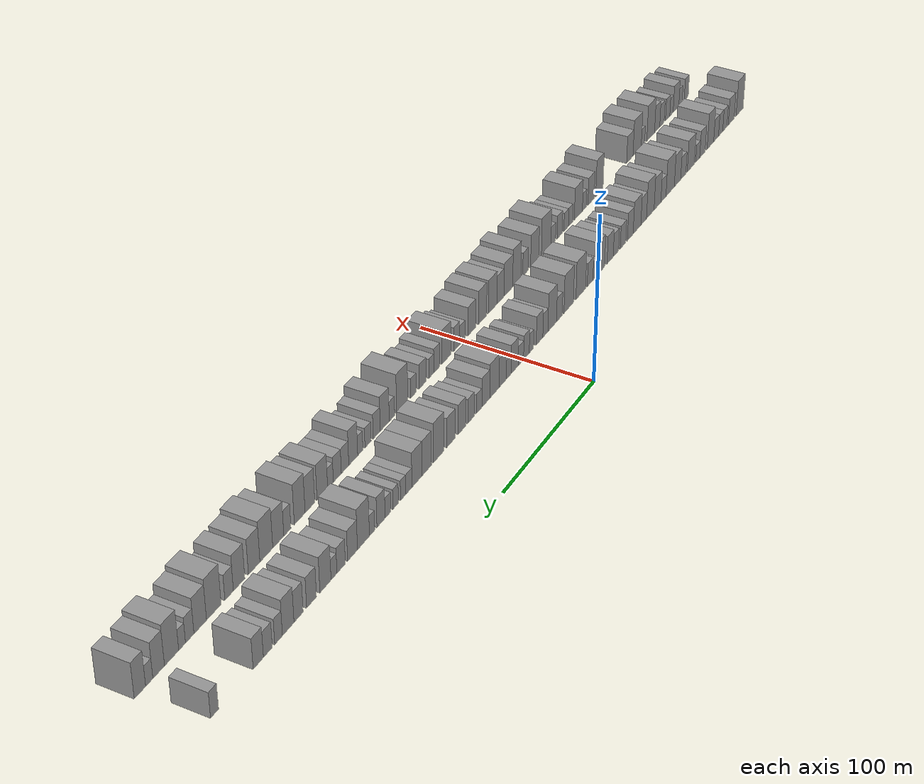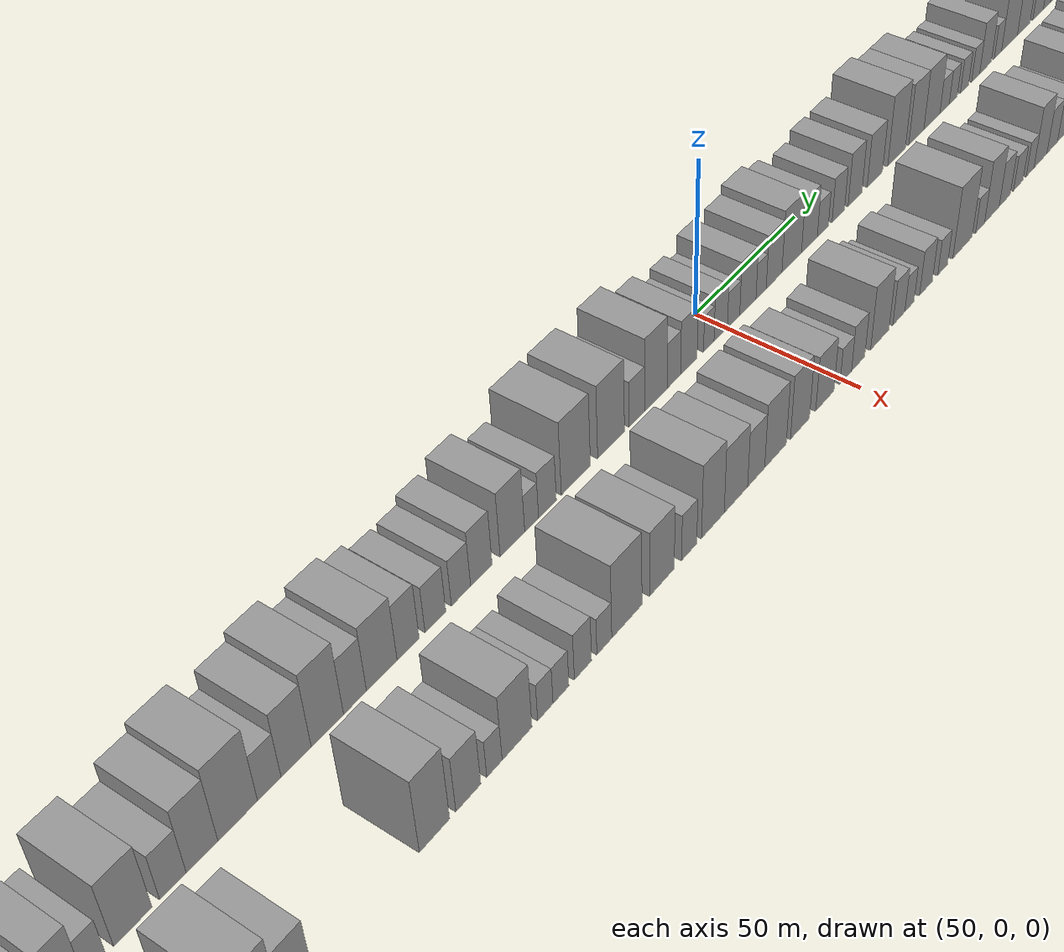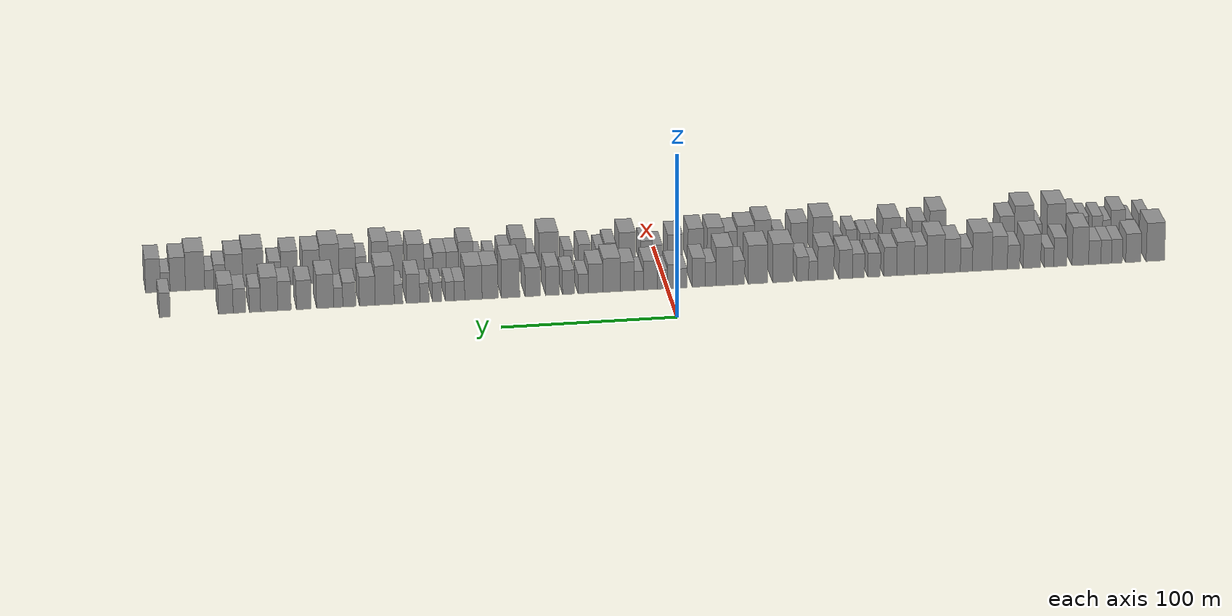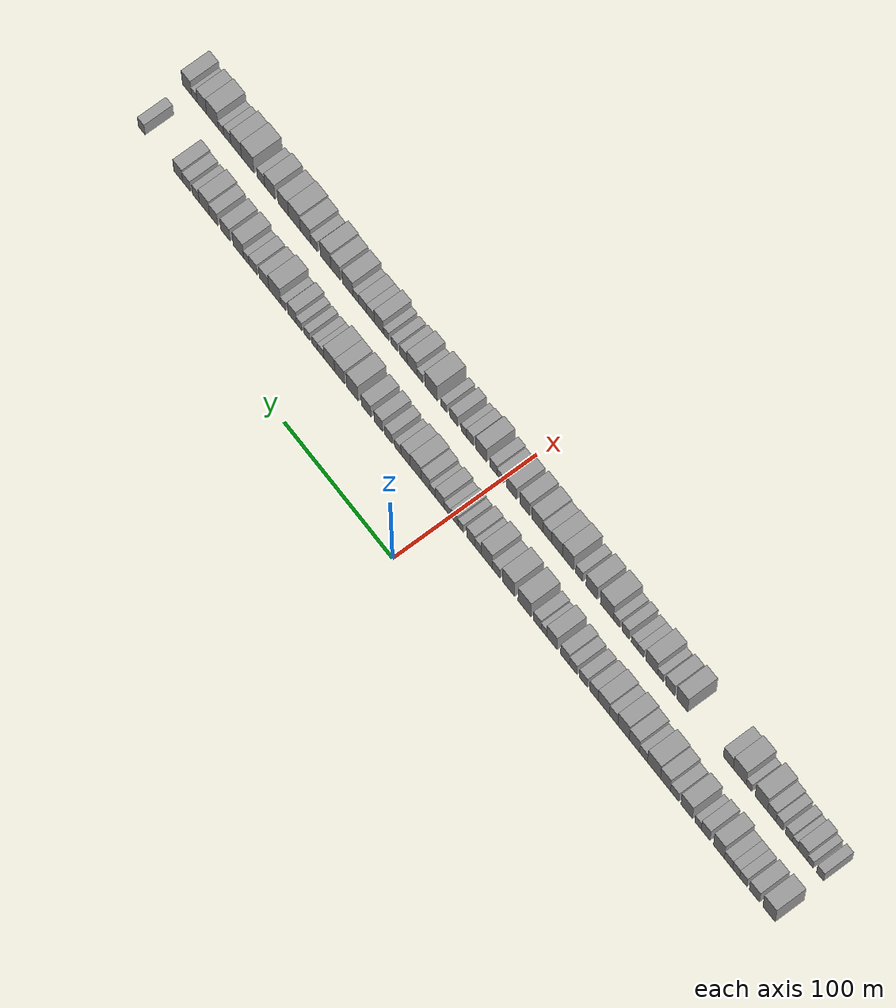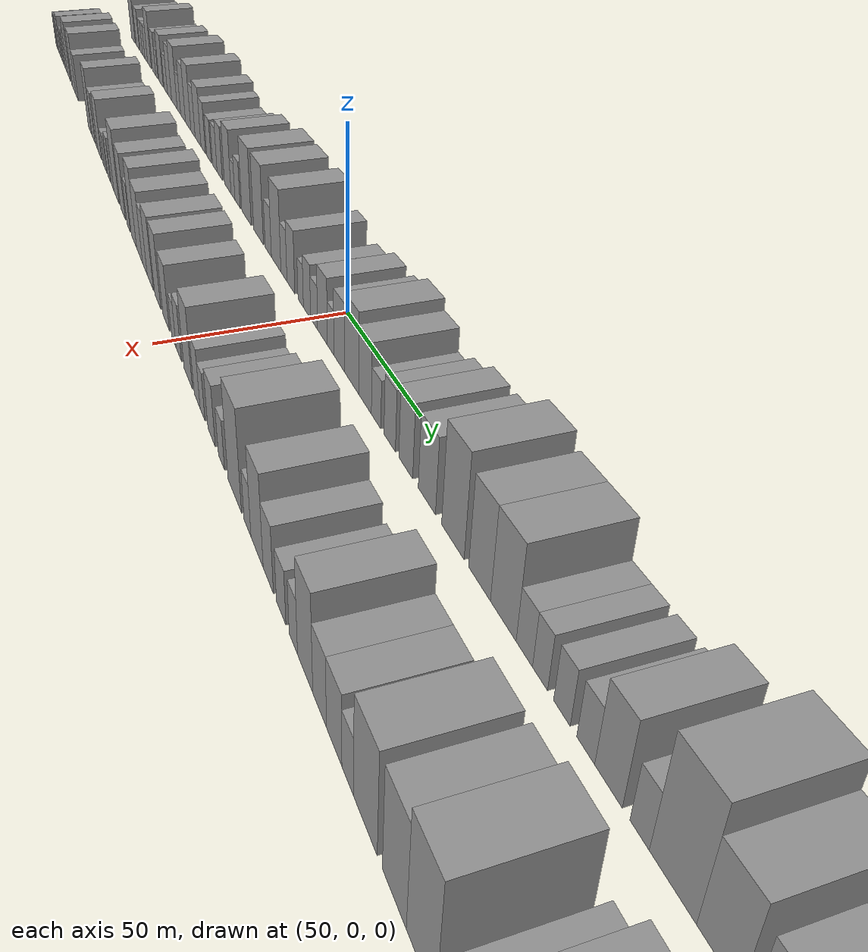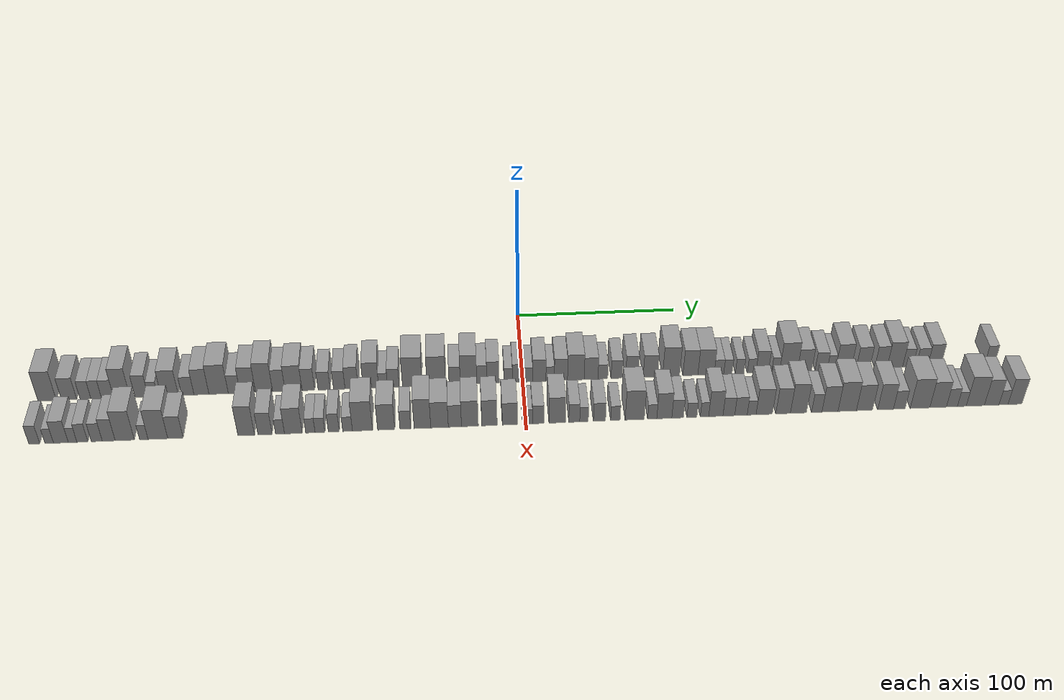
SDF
<sdf version="1.6">
 <world name="default">
  <scene>
   <sky><clouds><speed>12</speed></clouds></sky>
   <ambient>0.4 0.4 0.4 1</ambient>
   <background>0.7 0.7 0.7 1</background>
   <shadows>1</shadows>
  </scene>
  <gravity>0 0 -9.8066</gravity>
  <magnetic_field>6e-06 2.3e-05 -4.2e-05</magnetic_field>
  <physics default="0" name="default_physics" type="ode">
   <ode>
    <solver>
     <type>quick</type>
     <iters>10</iters>
     <sor>1.0</sor>
     <use_dynamic_moi_rescaling>0</use_dynamic_moi_rescaling>
    </solver>
    <constraints>
     <cfm>0</cfm>
     <erp>0.2</erp>
     <contact_max_correcting_vel>100</contact_max_correcting_vel>
     <contact_surface_layer>0.001</contact_surface_layer>
    </constraints>
   </ode>
   <max_step_size>0.004</max_step_size>
   <real_time_factor>1</real_time_factor>
   <real_time_update_rate>250</real_time_update_rate>
  </physics>
  <light name="sun" type="directional">
   <pose>0 0 10 0 0 0</pose>
   <diffuse>0.8 0.8 0.8 1</diffuse>
   <specular>0.2 0.2 0.2 1</specular>
   <attenuation>
    <range>1000</range>
    <constant>0.9</constant>
    <linear>0.01</linear>
    <quadratic>0.001</quadratic>
   </attenuation>
   <direction>-0.5 0.1 -0.9</direction>
  </light>
  <model name="building_1">
   <static>1</static>
   <pose>50.0000 -284.5758 0 0.000000 0.000000 0.000000</pose>
   <link name="link">
    <pose>0 0 12.00 0 0 0</pose>
    <collision name="collision"><geometry><box><size>20.0000 10.8484 24.0000</size></box></geometry></collision>
    <visual name="visual">
     <cast_shadows>0</cast_shadows>
     <geometry><box><size>20.0000 10.8484 24.0000</size></box></geometry>
     <material>
      <script>
       <uri>model://grey_wall/materials/scripts</uri>
       <uri>model://grey_wall/materials/textures</uri>
       <name>vrc/grey_wall</name>
      </script>
     </material>
    </visual>
   </link>
  </model>
  <model name="building_2">
   <static>1</static>
   <pose>50.0000 -271.6562 0 0.000000 0.000000 0.000000</pose>
   <link name="link">
    <pose>0 0 9.00 0 0 0</pose>
    <collision name="collision"><geometry><box><size>20.0000 8.9907 18.0000</size></box></geometry></collision>
    <visual name="visual">
     <cast_shadows>0</cast_shadows>
     <geometry><box><size>20.0000 8.9907 18.0000</size></box></geometry>
     <material>
      <script>
       <uri>model://grey_wall/materials/scripts</uri>
       <uri>model://grey_wall/materials/textures</uri>
       <name>vrc/grey_wall</name>
      </script>
     </material>
    </visual>
   </link>
  </model>
  <model name="building_3">
   <static>1</static>
   <pose>50.0000 -261.9601 0 0.000000 0.000000 0.000000</pose>
   <link name="link">
    <pose>0 0 7.50 0 0 0</pose>
    <collision name="collision"><geometry><box><size>20.0000 6.4016 15.0000</size></box></geometry></collision>
    <visual name="visual">
     <cast_shadows>0</cast_shadows>
     <geometry><box><size>20.0000 6.4016 15.0000</size></box></geometry>
     <material>
      <script>
       <uri>model://grey_wall/materials/scripts</uri>
       <uri>model://grey_wall/materials/textures</uri>
       <name>vrc/grey_wall</name>
      </script>
     </material>
    </visual>
   </link>
  </model>
  <model name="building_4">
   <static>1</static>
   <pose>50.0000 -255.6335 0 0.000000 0.000000 0.000000</pose>
   <link name="link">
    <pose>0 0 7.50 0 0 0</pose>
    <collision name="collision"><geometry><box><size>20.0000 6.2517 15.0000</size></box></geometry></collision>
    <visual name="visual">
     <cast_shadows>0</cast_shadows>
     <geometry><box><size>20.0000 6.2517 15.0000</size></box></geometry>
     <material>
      <script>
       <uri>model://grey_wall/materials/scripts</uri>
       <uri>model://grey_wall/materials/textures</uri>
       <name>vrc/grey_wall</name>
      </script>
     </material>
    </visual>
   </link>
  </model>
  <model name="building_5">
   <static>1</static>
   <pose>50.0000 -248.9060 0 0.000000 0.000000 0.000000</pose>
   <link name="link">
    <pose>0 0 7.50 0 0 0</pose>
    <collision name="collision"><geometry><box><size>20.0000 7.2034 15.0000</size></box></geometry></collision>
    <visual name="visual">
     <cast_shadows>0</cast_shadows>
     <geometry><box><size>20.0000 7.2034 15.0000</size></box></geometry>
     <material>
      <script>
       <uri>model://grey_wall/materials/scripts</uri>
       <uri>model://grey_wall/materials/textures</uri>
       <name>vrc/grey_wall</name>
      </script>
     </material>
    </visual>
   </link>
  </model>
  <model name="building_6">
   <static>1</static>
   <pose>50.0000 -240.4666 0 0.000000 0.000000 0.000000</pose>
   <link name="link">
    <pose>0 0 12.00 0 0 0</pose>
    <collision name="collision"><geometry><box><size>20.0000 9.6754 24.0000</size></box></geometry></collision>
    <visual name="visual">
     <cast_shadows>0</cast_shadows>
     <geometry><box><size>20.0000 9.6754 24.0000</size></box></geometry>
     <material>
      <script>
       <uri>model://grey_wall/materials/scripts</uri>
       <uri>model://grey_wall/materials/textures</uri>
       <name>vrc/grey_wall</name>
      </script>
     </material>
    </visual>
   </link>
  </model>
  <model name="building_7">
   <static>1</static>
   <pose>50.0000 -228.7247 0 0.000000 0.000000 0.000000</pose>
   <link name="link">
    <pose>0 0 9.00 0 0 0</pose>
    <collision name="collision"><geometry><box><size>20.0000 7.8084 18.0000</size></box></geometry></collision>
    <visual name="visual">
     <cast_shadows>0</cast_shadows>
     <geometry><box><size>20.0000 7.8084 18.0000</size></box></geometry>
     <material>
      <script>
       <uri>model://grey_wall/materials/scripts</uri>
       <uri>model://grey_wall/materials/textures</uri>
       <name>vrc/grey_wall</name>
      </script>
     </material>
    </visual>
   </link>
  </model>
  <model name="building_8">
   <static>1</static>
   <pose>50.0000 -221.9876 0 0.000000 0.000000 0.000000</pose>
   <link name="link">
    <pose>0 0 6.00 0 0 0</pose>
    <collision name="collision"><geometry><box><size>20.0000 5.6657 12.0000</size></box></geometry></collision>
    <visual name="visual">
     <cast_shadows>0</cast_shadows>
     <geometry><box><size>20.0000 5.6657 12.0000</size></box></geometry>
     <material>
      <script>
       <uri>model://grey_wall/materials/scripts</uri>
       <uri>model://grey_wall/materials/textures</uri>
       <name>vrc/grey_wall</name>
      </script>
     </material>
    </visual>
   </link>
  </model>
  <model name="building_9">
   <static>1</static>
   <pose>50.0000 -212.0377 0 0.000000 0.000000 0.000000</pose>
   <link name="link">
    <pose>0 0 10.50 0 0 0</pose>
    <collision name="collision"><geometry><box><size>20.0000 10.2342 21.0000</size></box></geometry></collision>
    <visual name="visual">
     <cast_shadows>0</cast_shadows>
     <geometry><box><size>20.0000 10.2342 21.0000</size></box></geometry>
     <material>
      <script>
       <uri>model://grey_wall/materials/scripts</uri>
       <uri>model://grey_wall/materials/textures</uri>
       <name>vrc/grey_wall</name>
      </script>
     </material>
    </visual>
   </link>
  </model>
  <model name="building_10">
   <static>1</static>
   <pose>50.0000 -201.2680 0 0.000000 0.000000 0.000000</pose>
   <link name="link">
    <pose>0 0 7.50 0 0 0</pose>
    <collision name="collision"><geometry><box><size>20.0000 7.3052 15.0000</size></box></geometry></collision>
    <visual name="visual">
     <cast_shadows>0</cast_shadows>
     <geometry><box><size>20.0000 7.3052 15.0000</size></box></geometry>
     <material>
      <script>
       <uri>model://grey_wall/materials/scripts</uri>
       <uri>model://grey_wall/materials/textures</uri>
       <name>vrc/grey_wall</name>
      </script>
     </material>
    </visual>
   </link>
  </model>
  <model name="building_11">
   <static>1</static>
   <pose>50.0000 -193.1629 0 0.000000 0.000000 0.000000</pose>
   <link name="link">
    <pose>0 0 10.50 0 0 0</pose>
    <collision name="collision"><geometry><box><size>20.0000 8.9050 21.0000</size></box></geometry></collision>
    <visual name="visual">
     <cast_shadows>0</cast_shadows>
     <geometry><box><size>20.0000 8.9050 21.0000</size></box></geometry>
     <material>
      <script>
       <uri>model://grey_wall/materials/scripts</uri>
       <uri>model://grey_wall/materials/textures</uri>
       <name>vrc/grey_wall</name>
      </script>
     </material>
    </visual>
   </link>
  </model>
  <model name="building_12">
   <static>1</static>
   <pose>50.0000 -182.9442 0 0.000000 0.000000 0.000000</pose>
   <link name="link">
    <pose>0 0 12.00 0 0 0</pose>
    <collision name="collision"><geometry><box><size>20.0000 11.5325 24.0000</size></box></geometry></collision>
    <visual name="visual">
     <cast_shadows>0</cast_shadows>
     <geometry><box><size>20.0000 11.5325 24.0000</size></box></geometry>
     <material>
      <script>
       <uri>model://grey_wall/materials/scripts</uri>
       <uri>model://grey_wall/materials/textures</uri>
       <name>vrc/grey_wall</name>
      </script>
     </material>
    </visual>
   </link>
  </model>
  <model name="building_13">
   <static>1</static>
   <pose>50.0000 -173.6545 0 0.000000 0.000000 0.000000</pose>
   <link name="link">
    <pose>0 0 7.50 0 0 0</pose>
    <collision name="collision"><geometry><box><size>20.0000 7.0468 15.0000</size></box></geometry></collision>
    <visual name="visual">
     <cast_shadows>0</cast_shadows>
     <geometry><box><size>20.0000 7.0468 15.0000</size></box></geometry>
     <material>
      <script>
       <uri>model://grey_wall/materials/scripts</uri>
       <uri>model://grey_wall/materials/textures</uri>
       <name>vrc/grey_wall</name>
      </script>
     </material>
    </visual>
   </link>
  </model>
  <model name="building_14">
   <static>1</static>
   <pose>50.0000 -165.5203 0 0.000000 0.000000 0.000000</pose>
   <link name="link">
    <pose>0 0 10.50 0 0 0</pose>
    <collision name="collision"><geometry><box><size>20.0000 9.2216 21.0000</size></box></geometry></collision>
    <visual name="visual">
     <cast_shadows>0</cast_shadows>
     <geometry><box><size>20.0000 9.2216 21.0000</size></box></geometry>
     <material>
      <script>
       <uri>model://grey_wall/materials/scripts</uri>
       <uri>model://grey_wall/materials/textures</uri>
       <name>vrc/grey_wall</name>
      </script>
     </material>
    </visual>
   </link>
  </model>
  <model name="building_15">
   <static>1</static>
   <pose>50.0000 -155.7967 0 0.000000 0.000000 0.000000</pose>
   <link name="link">
    <pose>0 0 12.00 0 0 0</pose>
    <collision name="collision"><geometry><box><size>20.0000 10.2256 24.0000</size></box></geometry></collision>
    <visual name="visual">
     <cast_shadows>0</cast_shadows>
     <geometry><box><size>20.0000 10.2256 24.0000</size></box></geometry>
     <material>
      <script>
       <uri>model://grey_wall/materials/scripts</uri>
       <uri>model://grey_wall/materials/textures</uri>
       <name>vrc/grey_wall</name>
      </script>
     </material>
    </visual>
   </link>
  </model>
  <model name="building_16">
   <static>1</static>
   <pose>50.0000 -146.9506 0 0.000000 0.000000 0.000000</pose>
   <link name="link">
    <pose>0 0 9.00 0 0 0</pose>
    <collision name="collision"><geometry><box><size>20.0000 7.4665 18.0000</size></box></geometry></collision>
    <visual name="visual">
     <cast_shadows>0</cast_shadows>
     <geometry><box><size>20.0000 7.4665 18.0000</size></box></geometry>
     <material>
      <script>
       <uri>model://grey_wall/materials/scripts</uri>
       <uri>model://grey_wall/materials/textures</uri>
       <name>vrc/grey_wall</name>
      </script>
     </material>
    </visual>
   </link>
  </model>
  <model name="building_17">
   <static>1</static>
   <pose>50.0000 -138.1325 0 0.000000 0.000000 0.000000</pose>
   <link name="link">
    <pose>0 0 10.50 0 0 0</pose>
    <collision name="collision"><geometry><box><size>20.0000 10.1697 21.0000</size></box></geometry></collision>
    <visual name="visual">
     <cast_shadows>0</cast_shadows>
     <geometry><box><size>20.0000 10.1697 21.0000</size></box></geometry>
     <material>
      <script>
       <uri>model://grey_wall/materials/scripts</uri>
       <uri>model://grey_wall/materials/textures</uri>
       <name>vrc/grey_wall</name>
      </script>
     </material>
    </visual>
   </link>
  </model>
  <model name="building_18">
   <static>1</static>
   <pose>50.0000 -129.2719 0 0.000000 0.000000 0.000000</pose>
   <link name="link">
    <pose>0 0 9.00 0 0 0</pose>
    <collision name="collision"><geometry><box><size>20.0000 7.5515 18.0000</size></box></geometry></collision>
    <visual name="visual">
     <cast_shadows>0</cast_shadows>
     <geometry><box><size>20.0000 7.5515 18.0000</size></box></geometry>
     <material>
      <script>
       <uri>model://grey_wall/materials/scripts</uri>
       <uri>model://grey_wall/materials/textures</uri>
       <name>vrc/grey_wall</name>
      </script>
     </material>
    </visual>
   </link>
  </model>
  <model name="building_19">
   <static>1</static>
   <pose>50.0000 -119.8560 0 0.000000 0.000000 0.000000</pose>
   <link name="link">
    <pose>0 0 7.50 0 0 0</pose>
    <collision name="collision"><geometry><box><size>20.0000 7.2804 15.0000</size></box></geometry></collision>
    <visual name="visual">
     <cast_shadows>0</cast_shadows>
     <geometry><box><size>20.0000 7.2804 15.0000</size></box></geometry>
     <material>
      <script>
       <uri>model://grey_wall/materials/scripts</uri>
       <uri>model://grey_wall/materials/textures</uri>
       <name>vrc/grey_wall</name>
      </script>
     </material>
    </visual>
   </link>
  </model>
  <model name="building_20">
   <static>1</static>
   <pose>50.0000 -110.7603 0 0.000000 0.000000 0.000000</pose>
   <link name="link">
    <pose>0 0 7.50 0 0 0</pose>
    <collision name="collision"><geometry><box><size>20.0000 6.9111 15.0000</size></box></geometry></collision>
    <visual name="visual">
     <cast_shadows>0</cast_shadows>
     <geometry><box><size>20.0000 6.9111 15.0000</size></box></geometry>
     <material>
      <script>
       <uri>model://grey_wall/materials/scripts</uri>
       <uri>model://grey_wall/materials/textures</uri>
       <name>vrc/grey_wall</name>
      </script>
     </material>
    </visual>
   </link>
  </model>
  <model name="building_21">
   <static>1</static>
   <pose>50.0000 -103.3472 0 0.000000 0.000000 0.000000</pose>
   <link name="link">
    <pose>0 0 9.00 0 0 0</pose>
    <collision name="collision"><geometry><box><size>20.0000 7.9150 18.0000</size></box></geometry></collision>
    <visual name="visual">
     <cast_shadows>0</cast_shadows>
     <geometry><box><size>20.0000 7.9150 18.0000</size></box></geometry>
     <material>
      <script>
       <uri>model://grey_wall/materials/scripts</uri>
       <uri>model://grey_wall/materials/textures</uri>
       <name>vrc/grey_wall</name>
      </script>
     </material>
    </visual>
   </link>
  </model>
  <model name="building_22">
   <static>1</static>
   <pose>50.0000 -91.7295 0 0.000000 0.000000 0.000000</pose>
   <link name="link">
    <pose>0 0 10.50 0 0 0</pose>
    <collision name="collision"><geometry><box><size>20.0000 9.3206 21.0000</size></box></geometry></collision>
    <visual name="visual">
     <cast_shadows>0</cast_shadows>
     <geometry><box><size>20.0000 9.3206 21.0000</size></box></geometry>
     <material>
      <script>
       <uri>model://grey_wall/materials/scripts</uri>
       <uri>model://grey_wall/materials/textures</uri>
       <name>vrc/grey_wall</name>
      </script>
     </material>
    </visual>
   </link>
  </model>
  <model name="building_23">
   <static>1</static>
   <pose>50.0000 -84.3872 0 0.000000 0.000000 0.000000</pose>
   <link name="link">
    <pose>0 0 6.00 0 0 0</pose>
    <collision name="collision"><geometry><box><size>20.0000 5.3639 12.0000</size></box></geometry></collision>
    <visual name="visual">
     <cast_shadows>0</cast_shadows>
     <geometry><box><size>20.0000 5.3639 12.0000</size></box></geometry>
     <material>
      <script>
       <uri>model://grey_wall/materials/scripts</uri>
       <uri>model://grey_wall/materials/textures</uri>
       <name>vrc/grey_wall</name>
      </script>
     </material>
    </visual>
   </link>
  </model>
  <model name="building_24">
   <static>1</static>
   <pose>50.0000 -78.2163 0 0.000000 0.000000 0.000000</pose>
   <link name="link">
    <pose>0 0 7.50 0 0 0</pose>
    <collision name="collision"><geometry><box><size>20.0000 6.9779 15.0000</size></box></geometry></collision>
    <visual name="visual">
     <cast_shadows>0</cast_shadows>
     <geometry><box><size>20.0000 6.9779 15.0000</size></box></geometry>
     <material>
      <script>
       <uri>model://grey_wall/materials/scripts</uri>
       <uri>model://grey_wall/materials/textures</uri>
       <name>vrc/grey_wall</name>
      </script>
     </material>
    </visual>
   </link>
  </model>
  <model name="building_25">
   <static>1</static>
   <pose>50.0000 -66.8264 0 0.000000 0.000000 0.000000</pose>
   <link name="link">
    <pose>0 0 12.00 0 0 0</pose>
    <collision name="collision"><geometry><box><size>20.0000 11.8019 24.0000</size></box></geometry></collision>
    <visual name="visual">
     <cast_shadows>0</cast_shadows>
     <geometry><box><size>20.0000 11.8019 24.0000</size></box></geometry>
     <material>
      <script>
       <uri>model://grey_wall/materials/scripts</uri>
       <uri>model://grey_wall/materials/textures</uri>
       <name>vrc/grey_wall</name>
      </script>
     </material>
    </visual>
   </link>
  </model>
  <model name="building_26">
   <static>1</static>
   <pose>50.0000 -52.2825 0 0.000000 0.000000 0.000000</pose>
   <link name="link">
    <pose>0 0 12.00 0 0 0</pose>
    <collision name="collision"><geometry><box><size>20.0000 11.2858 24.0000</size></box></geometry></collision>
    <visual name="visual">
     <cast_shadows>0</cast_shadows>
     <geometry><box><size>20.0000 11.2858 24.0000</size></box></geometry>
     <material>
      <script>
       <uri>model://grey_wall/materials/scripts</uri>
       <uri>model://grey_wall/materials/textures</uri>
       <name>vrc/grey_wall</name>
      </script>
     </material>
    </visual>
   </link>
  </model>
  <model name="building_27">
   <static>1</static>
   <pose>50.0000 -41.2421 0 0.000000 0.000000 0.000000</pose>
   <link name="link">
    <pose>0 0 7.50 0 0 0</pose>
    <collision name="collision"><geometry><box><size>20.0000 6.7951 15.0000</size></box></geometry></collision>
    <visual name="visual">
     <cast_shadows>0</cast_shadows>
     <geometry><box><size>20.0000 6.7951 15.0000</size></box></geometry>
     <material>
      <script>
       <uri>model://grey_wall/materials/scripts</uri>
       <uri>model://grey_wall/materials/textures</uri>
       <name>vrc/grey_wall</name>
      </script>
     </material>
    </visual>
   </link>
  </model>
  <model name="building_28">
   <static>1</static>
   <pose>50.0000 -32.8636 0 0.000000 0.000000 0.000000</pose>
   <link name="link">
    <pose>0 0 12.00 0 0 0</pose>
    <collision name="collision"><geometry><box><size>20.0000 9.9619 24.0000</size></box></geometry></collision>
    <visual name="visual">
     <cast_shadows>0</cast_shadows>
     <geometry><box><size>20.0000 9.9619 24.0000</size></box></geometry>
     <material>
      <script>
       <uri>model://grey_wall/materials/scripts</uri>
       <uri>model://grey_wall/materials/textures</uri>
       <name>vrc/grey_wall</name>
      </script>
     </material>
    </visual>
   </link>
  </model>
  <model name="building_29">
   <static>1</static>
   <pose>50.0000 -24.8612 0 0.000000 0.000000 0.000000</pose>
   <link name="link">
    <pose>0 0 7.50 0 0 0</pose>
    <collision name="collision"><geometry><box><size>20.0000 6.0428 15.0000</size></box></geometry></collision>
    <visual name="visual">
     <cast_shadows>0</cast_shadows>
     <geometry><box><size>20.0000 6.0428 15.0000</size></box></geometry>
     <material>
      <script>
       <uri>model://grey_wall/materials/scripts</uri>
       <uri>model://grey_wall/materials/textures</uri>
       <name>vrc/grey_wall</name>
      </script>
     </material>
    </visual>
   </link>
  </model>
  <model name="building_30">
   <static>1</static>
   <pose>50.0000 -18.0613 0 0.000000 0.000000 0.000000</pose>
   <link name="link">
    <pose>0 0 9.00 0 0 0</pose>
    <collision name="collision"><geometry><box><size>20.0000 7.5571 18.0000</size></box></geometry></collision>
    <visual name="visual">
     <cast_shadows>0</cast_shadows>
     <geometry><box><size>20.0000 7.5571 18.0000</size></box></geometry>
     <material>
      <script>
       <uri>model://grey_wall/materials/scripts</uri>
       <uri>model://grey_wall/materials/textures</uri>
       <name>vrc/grey_wall</name>
      </script>
     </material>
    </visual>
   </link>
  </model>
  <model name="building_31">
   <static>1</static>
   <pose>50.0000 -8.8151 0 0.000000 0.000000 0.000000</pose>
   <link name="link">
    <pose>0 0 6.00 0 0 0</pose>
    <collision name="collision"><geometry><box><size>20.0000 4.9353 12.0000</size></box></geometry></collision>
    <visual name="visual">
     <cast_shadows>0</cast_shadows>
     <geometry><box><size>20.0000 4.9353 12.0000</size></box></geometry>
     <material>
      <script>
       <uri>model://grey_wall/materials/scripts</uri>
       <uri>model://grey_wall/materials/textures</uri>
       <name>vrc/grey_wall</name>
      </script>
     </material>
    </visual>
   </link>
  </model>
  <model name="building_32">
   <static>1</static>
   <pose>50.0000 -3.1559 0 0.000000 0.000000 0.000000</pose>
   <link name="link">
    <pose>0 0 7.50 0 0 0</pose>
    <collision name="collision"><geometry><box><size>20.0000 6.3832 15.0000</size></box></geometry></collision>
    <visual name="visual">
     <cast_shadows>0</cast_shadows>
     <geometry><box><size>20.0000 6.3832 15.0000</size></box></geometry>
     <material>
      <script>
       <uri>model://grey_wall/materials/scripts</uri>
       <uri>model://grey_wall/materials/textures</uri>
       <name>vrc/grey_wall</name>
      </script>
     </material>
    </visual>
   </link>
  </model>
  <model name="building_33">
   <static>1</static>
   <pose>50.0000 3.0091 0 0.000000 0.000000 0.000000</pose>
   <link name="link">
    <pose>0 0 6.00 0 0 0</pose>
    <collision name="collision"><geometry><box><size>20.0000 5.9468 12.0000</size></box></geometry></collision>
    <visual name="visual">
     <cast_shadows>0</cast_shadows>
     <geometry><box><size>20.0000 5.9468 12.0000</size></box></geometry>
     <material>
      <script>
       <uri>model://grey_wall/materials/scripts</uri>
       <uri>model://grey_wall/materials/textures</uri>
       <name>vrc/grey_wall</name>
      </script>
     </material>
    </visual>
   </link>
  </model>
  <model name="building_34">
   <static>1</static>
   <pose>50.0000 9.9899 0 0.000000 0.000000 0.000000</pose>
   <link name="link">
    <pose>0 0 9.00 0 0 0</pose>
    <collision name="collision"><geometry><box><size>20.0000 8.0147 18.0000</size></box></geometry></collision>
    <visual name="visual">
     <cast_shadows>0</cast_shadows>
     <geometry><box><size>20.0000 8.0147 18.0000</size></box></geometry>
     <material>
      <script>
       <uri>model://grey_wall/materials/scripts</uri>
       <uri>model://grey_wall/materials/textures</uri>
       <name>vrc/grey_wall</name>
      </script>
     </material>
    </visual>
   </link>
  </model>
  <model name="building_35">
   <static>1</static>
   <pose>50.0000 16.5669 0 0.000000 0.000000 0.000000</pose>
   <link name="link">
    <pose>0 0 6.00 0 0 0</pose>
    <collision name="collision"><geometry><box><size>20.0000 5.1393 12.0000</size></box></geometry></collision>
    <visual name="visual">
     <cast_shadows>0</cast_shadows>
     <geometry><box><size>20.0000 5.1393 12.0000</size></box></geometry>
     <material>
      <script>
       <uri>model://grey_wall/materials/scripts</uri>
       <uri>model://grey_wall/materials/textures</uri>
       <name>vrc/grey_wall</name>
      </script>
     </material>
    </visual>
   </link>
  </model>
  <model name="building_36">
   <static>1</static>
   <pose>50.0000 23.1288 0 0.000000 0.000000 0.000000</pose>
   <link name="link">
    <pose>0 0 9.00 0 0 0</pose>
    <collision name="collision"><geometry><box><size>20.0000 7.9845 18.0000</size></box></geometry></collision>
    <visual name="visual">
     <cast_shadows>0</cast_shadows>
     <geometry><box><size>20.0000 7.9845 18.0000</size></box></geometry>
     <material>
      <script>
       <uri>model://grey_wall/materials/scripts</uri>
       <uri>model://grey_wall/materials/textures</uri>
       <name>vrc/grey_wall</name>
      </script>
     </material>
    </visual>
   </link>
  </model>
  <model name="building_37">
   <static>1</static>
   <pose>50.0000 32.1885 0 0.000000 0.000000 0.000000</pose>
   <link name="link">
    <pose>0 0 10.50 0 0 0</pose>
    <collision name="collision"><geometry><box><size>20.0000 10.1349 21.0000</size></box></geometry></collision>
    <visual name="visual">
     <cast_shadows>0</cast_shadows>
     <geometry><box><size>20.0000 10.1349 21.0000</size></box></geometry>
     <material>
      <script>
       <uri>model://grey_wall/materials/scripts</uri>
       <uri>model://grey_wall/materials/textures</uri>
       <name>vrc/grey_wall</name>
      </script>
     </material>
    </visual>
   </link>
  </model>
  <model name="building_38">
   <static>1</static>
   <pose>50.0000 41.4720 0 0.000000 0.000000 0.000000</pose>
   <link name="link">
    <pose>0 0 9.00 0 0 0</pose>
    <collision name="collision"><geometry><box><size>20.0000 8.4321 18.0000</size></box></geometry></collision>
    <visual name="visual">
     <cast_shadows>0</cast_shadows>
     <geometry><box><size>20.0000 8.4321 18.0000</size></box></geometry>
     <material>
      <script>
       <uri>model://grey_wall/materials/scripts</uri>
       <uri>model://grey_wall/materials/textures</uri>
       <name>vrc/grey_wall</name>
      </script>
     </material>
    </visual>
   </link>
  </model>
  <model name="building_39">
   <static>1</static>
   <pose>50.0000 48.6696 0 0.000000 0.000000 0.000000</pose>
   <link name="link">
    <pose>0 0 6.00 0 0 0</pose>
    <collision name="collision"><geometry><box><size>20.0000 5.9631 12.0000</size></box></geometry></collision>
    <visual name="visual">
     <cast_shadows>0</cast_shadows>
     <geometry><box><size>20.0000 5.9631 12.0000</size></box></geometry>
     <material>
      <script>
       <uri>model://grey_wall/materials/scripts</uri>
       <uri>model://grey_wall/materials/textures</uri>
       <name>vrc/grey_wall</name>
      </script>
     </material>
    </visual>
   </link>
  </model>
  <model name="building_40">
   <static>1</static>
   <pose>50.0000 57.0762 0 0.000000 0.000000 0.000000</pose>
   <link name="link">
    <pose>0 0 7.50 0 0 0</pose>
    <collision name="collision"><geometry><box><size>20.0000 6.8501 15.0000</size></box></geometry></collision>
    <visual name="visual">
     <cast_shadows>0</cast_shadows>
     <geometry><box><size>20.0000 6.8501 15.0000</size></box></geometry>
     <material>
      <script>
       <uri>model://grey_wall/materials/scripts</uri>
       <uri>model://grey_wall/materials/textures</uri>
       <name>vrc/grey_wall</name>
      </script>
     </material>
    </visual>
   </link>
  </model>
  <model name="building_41">
   <static>1</static>
   <pose>50.0000 66.3789 0 0.000000 0.000000 0.000000</pose>
   <link name="link">
    <pose>0 0 9.00 0 0 0</pose>
    <collision name="collision"><geometry><box><size>20.0000 7.7553 18.0000</size></box></geometry></collision>
    <visual name="visual">
     <cast_shadows>0</cast_shadows>
     <geometry><box><size>20.0000 7.7553 18.0000</size></box></geometry>
     <material>
      <script>
       <uri>model://grey_wall/materials/scripts</uri>
       <uri>model://grey_wall/materials/textures</uri>
       <name>vrc/grey_wall</name>
      </script>
     </material>
    </visual>
   </link>
  </model>
  <model name="building_42">
   <static>1</static>
   <pose>50.0000 77.6829 0 0.000000 0.000000 0.000000</pose>
   <link name="link">
    <pose>0 0 9.00 0 0 0</pose>
    <collision name="collision"><geometry><box><size>20.0000 8.8527 18.0000</size></box></geometry></collision>
    <visual name="visual">
     <cast_shadows>0</cast_shadows>
     <geometry><box><size>20.0000 8.8527 18.0000</size></box></geometry>
     <material>
      <script>
       <uri>model://grey_wall/materials/scripts</uri>
       <uri>model://grey_wall/materials/textures</uri>
       <name>vrc/grey_wall</name>
      </script>
     </material>
    </visual>
   </link>
  </model>
  <model name="building_43">
   <static>1</static>
   <pose>50.0000 90.3405 0 0.000000 0.000000 0.000000</pose>
   <link name="link">
    <pose>0 0 12.00 0 0 0</pose>
    <collision name="collision"><geometry><box><size>20.0000 10.4624 24.0000</size></box></geometry></collision>
    <visual name="visual">
     <cast_shadows>0</cast_shadows>
     <geometry><box><size>20.0000 10.4624 24.0000</size></box></geometry>
     <material>
      <script>
       <uri>model://grey_wall/materials/scripts</uri>
       <uri>model://grey_wall/materials/textures</uri>
       <name>vrc/grey_wall</name>
      </script>
     </material>
    </visual>
   </link>
  </model>
  <model name="building_44">
   <static>1</static>
   <pose>50.0000 102.1634 0 0.000000 0.000000 0.000000</pose>
   <link name="link">
    <pose>0 0 10.50 0 0 0</pose>
    <collision name="collision"><geometry><box><size>20.0000 9.1836 21.0000</size></box></geometry></collision>
    <visual name="visual">
     <cast_shadows>0</cast_shadows>
     <geometry><box><size>20.0000 9.1836 21.0000</size></box></geometry>
     <material>
      <script>
       <uri>model://grey_wall/materials/scripts</uri>
       <uri>model://grey_wall/materials/textures</uri>
       <name>vrc/grey_wall</name>
      </script>
     </material>
    </visual>
   </link>
  </model>
  <model name="building_45">
   <static>1</static>
   <pose>50.0000 111.7357 0 0.000000 0.000000 0.000000</pose>
   <link name="link">
    <pose>0 0 10.50 0 0 0</pose>
    <collision name="collision"><geometry><box><size>20.0000 9.9609 21.0000</size></box></geometry></collision>
    <visual name="visual">
     <cast_shadows>0</cast_shadows>
     <geometry><box><size>20.0000 9.9609 21.0000</size></box></geometry>
     <material>
      <script>
       <uri>model://grey_wall/materials/scripts</uri>
       <uri>model://grey_wall/materials/textures</uri>
       <name>vrc/grey_wall</name>
      </script>
     </material>
    </visual>
   </link>
  </model>
  <model name="building_46">
   <static>1</static>
   <pose>50.0000 119.6706 0 0.000000 0.000000 0.000000</pose>
   <link name="link">
    <pose>0 0 6.00 0 0 0</pose>
    <collision name="collision"><geometry><box><size>20.0000 5.9090 12.0000</size></box></geometry></collision>
    <visual name="visual">
     <cast_shadows>0</cast_shadows>
     <geometry><box><size>20.0000 5.9090 12.0000</size></box></geometry>
     <material>
      <script>
       <uri>model://grey_wall/materials/scripts</uri>
       <uri>model://grey_wall/materials/textures</uri>
       <name>vrc/grey_wall</name>
      </script>
     </material>
    </visual>
   </link>
  </model>
  <model name="building_47">
   <static>1</static>
   <pose>50.0000 125.2024 0 0.000000 0.000000 0.000000</pose>
   <link name="link">
    <pose>0 0 6.00 0 0 0</pose>
    <collision name="collision"><geometry><box><size>20.0000 5.1546 12.0000</size></box></geometry></collision>
    <visual name="visual">
     <cast_shadows>0</cast_shadows>
     <geometry><box><size>20.0000 5.1546 12.0000</size></box></geometry>
     <material>
      <script>
       <uri>model://grey_wall/materials/scripts</uri>
       <uri>model://grey_wall/materials/textures</uri>
       <name>vrc/grey_wall</name>
      </script>
     </material>
    </visual>
   </link>
  </model>
  <model name="building_48">
   <static>1</static>
   <pose>50.0000 132.4311 0 0.000000 0.000000 0.000000</pose>
   <link name="link">
    <pose>0 0 6.00 0 0 0</pose>
    <collision name="collision"><geometry><box><size>20.0000 5.3028 12.0000</size></box></geometry></collision>
    <visual name="visual">
     <cast_shadows>0</cast_shadows>
     <geometry><box><size>20.0000 5.3028 12.0000</size></box></geometry>
     <material>
      <script>
       <uri>model://grey_wall/materials/scripts</uri>
       <uri>model://grey_wall/materials/textures</uri>
       <name>vrc/grey_wall</name>
      </script>
     </material>
    </visual>
   </link>
  </model>
  <model name="building_49">
   <static>1</static>
   <pose>50.0000 139.7467 0 0.000000 0.000000 0.000000</pose>
   <link name="link">
    <pose>0 0 6.00 0 0 0</pose>
    <collision name="collision"><geometry><box><size>20.0000 5.3285 12.0000</size></box></geometry></collision>
    <visual name="visual">
     <cast_shadows>0</cast_shadows>
     <geometry><box><size>20.0000 5.3285 12.0000</size></box></geometry>
     <material>
      <script>
       <uri>model://grey_wall/materials/scripts</uri>
       <uri>model://grey_wall/materials/textures</uri>
       <name>vrc/grey_wall</name>
      </script>
     </material>
    </visual>
   </link>
  </model>
  <model name="building_50">
   <static>1</static>
   <pose>50.0000 146.2451 0 0.000000 0.000000 0.000000</pose>
   <link name="link">
    <pose>0 0 9.00 0 0 0</pose>
    <collision name="collision"><geometry><box><size>20.0000 7.6682 18.0000</size></box></geometry></collision>
    <visual name="visual">
     <cast_shadows>0</cast_shadows>
     <geometry><box><size>20.0000 7.6682 18.0000</size></box></geometry>
     <material>
      <script>
       <uri>model://grey_wall/materials/scripts</uri>
       <uri>model://grey_wall/materials/textures</uri>
       <name>vrc/grey_wall</name>
      </script>
     </material>
    </visual>
   </link>
  </model>
  <model name="building_51">
   <static>1</static>
   <pose>50.0000 154.5359 0 0.000000 0.000000 0.000000</pose>
   <link name="link">
    <pose>0 0 6.00 0 0 0</pose>
    <collision name="collision"><geometry><box><size>20.0000 4.9134 12.0000</size></box></geometry></collision>
    <visual name="visual">
     <cast_shadows>0</cast_shadows>
     <geometry><box><size>20.0000 4.9134 12.0000</size></box></geometry>
     <material>
      <script>
       <uri>model://grey_wall/materials/scripts</uri>
       <uri>model://grey_wall/materials/textures</uri>
       <name>vrc/grey_wall</name>
      </script>
     </material>
    </visual>
   </link>
  </model>
  <model name="building_52">
   <static>1</static>
   <pose>50.0000 162.4656 0 0.000000 0.000000 0.000000</pose>
   <link name="link">
    <pose>0 0 12.00 0 0 0</pose>
    <collision name="collision"><geometry><box><size>20.0000 10.9461 24.0000</size></box></geometry></collision>
    <visual name="visual">
     <cast_shadows>0</cast_shadows>
     <geometry><box><size>20.0000 10.9461 24.0000</size></box></geometry>
     <material>
      <script>
       <uri>model://grey_wall/materials/scripts</uri>
       <uri>model://grey_wall/materials/textures</uri>
       <name>vrc/grey_wall</name>
      </script>
     </material>
    </visual>
   </link>
  </model>
  <model name="building_53">
   <static>1</static>
   <pose>50.0000 172.4119 0 0.000000 0.000000 0.000000</pose>
   <link name="link">
    <pose>0 0 9.00 0 0 0</pose>
    <collision name="collision"><geometry><box><size>20.0000 8.9465 18.0000</size></box></geometry></collision>
    <visual name="visual">
     <cast_shadows>0</cast_shadows>
     <geometry><box><size>20.0000 8.9465 18.0000</size></box></geometry>
     <material>
      <script>
       <uri>model://grey_wall/materials/scripts</uri>
       <uri>model://grey_wall/materials/textures</uri>
       <name>vrc/grey_wall</name>
      </script>
     </material>
    </visual>
   </link>
  </model>
  <model name="building_54">
   <static>1</static>
   <pose>50.0000 182.6342 0 0.000000 0.000000 0.000000</pose>
   <link name="link">
    <pose>0 0 7.50 0 0 0</pose>
    <collision name="collision"><geometry><box><size>20.0000 7.4980 15.0000</size></box></geometry></collision>
    <visual name="visual">
     <cast_shadows>0</cast_shadows>
     <geometry><box><size>20.0000 7.4980 15.0000</size></box></geometry>
     <material>
      <script>
       <uri>model://grey_wall/materials/scripts</uri>
       <uri>model://grey_wall/materials/textures</uri>
       <name>vrc/grey_wall</name>
      </script>
     </material>
    </visual>
   </link>
  </model>
  <model name="building_55">
   <static>1</static>
   <pose>50.0000 188.9912 0 0.000000 0.000000 0.000000</pose>
   <link name="link">
    <pose>0 0 6.00 0 0 0</pose>
    <collision name="collision"><geometry><box><size>20.0000 5.2160 12.0000</size></box></geometry></collision>
    <visual name="visual">
     <cast_shadows>0</cast_shadows>
     <geometry><box><size>20.0000 5.2160 12.0000</size></box></geometry>
     <material>
      <script>
       <uri>model://grey_wall/materials/scripts</uri>
       <uri>model://grey_wall/materials/textures</uri>
       <name>vrc/grey_wall</name>
      </script>
     </material>
    </visual>
   </link>
  </model>
  <model name="building_56">
   <static>1</static>
   <pose>50.0000 196.4564 0 0.000000 0.000000 0.000000</pose>
   <link name="link">
    <pose>0 0 10.50 0 0 0</pose>
    <collision name="collision"><geometry><box><size>20.0000 9.7144 21.0000</size></box></geometry></collision>
    <visual name="visual">
     <cast_shadows>0</cast_shadows>
     <geometry><box><size>20.0000 9.7144 21.0000</size></box></geometry>
     <material>
      <script>
       <uri>model://grey_wall/materials/scripts</uri>
       <uri>model://grey_wall/materials/textures</uri>
       <name>vrc/grey_wall</name>
      </script>
     </material>
    </visual>
   </link>
  </model>
  <model name="building_57">
   <static>1</static>
   <pose>50.0000 208.5460 0 0.000000 0.000000 0.000000</pose>
   <link name="link">
    <pose>0 0 9.00 0 0 0</pose>
    <collision name="collision"><geometry><box><size>20.0000 8.4648 18.0000</size></box></geometry></collision>
    <visual name="visual">
     <cast_shadows>0</cast_shadows>
     <geometry><box><size>20.0000 8.4648 18.0000</size></box></geometry>
     <material>
      <script>
       <uri>model://grey_wall/materials/scripts</uri>
       <uri>model://grey_wall/materials/textures</uri>
       <name>vrc/grey_wall</name>
      </script>
     </material>
    </visual>
   </link>
  </model>
  <model name="building_58">
   <static>1</static>
   <pose>50.0000 219.6300 0 0.000000 0.000000 0.000000</pose>
   <link name="link">
    <pose>0 0 9.00 0 0 0</pose>
    <collision name="collision"><geometry><box><size>20.0000 7.7032 18.0000</size></box></geometry></collision>
    <visual name="visual">
     <cast_shadows>0</cast_shadows>
     <geometry><box><size>20.0000 7.7032 18.0000</size></box></geometry>
     <material>
      <script>
       <uri>model://grey_wall/materials/scripts</uri>
       <uri>model://grey_wall/materials/textures</uri>
       <name>vrc/grey_wall</name>
      </script>
     </material>
    </visual>
   </link>
  </model>
  <model name="building_59">
   <static>1</static>
   <pose>50.0000 228.3242 0 0.000000 0.000000 0.000000</pose>
   <link name="link">
    <pose>0 0 10.50 0 0 0</pose>
    <collision name="collision"><geometry><box><size>20.0000 9.6851 21.0000</size></box></geometry></collision>
    <visual name="visual">
     <cast_shadows>0</cast_shadows>
     <geometry><box><size>20.0000 9.6851 21.0000</size></box></geometry>
     <material>
      <script>
       <uri>model://grey_wall/materials/scripts</uri>
       <uri>model://grey_wall/materials/textures</uri>
       <name>vrc/grey_wall</name>
      </script>
     </material>
    </visual>
   </link>
  </model>
  <model name="building_60">
   <static>1</static>
   <pose>50.0000 236.3449 0 0.000000 0.000000 0.000000</pose>
   <link name="link">
    <pose>0 0 7.50 0 0 0</pose>
    <collision name="collision"><geometry><box><size>20.0000 6.3562 15.0000</size></box></geometry></collision>
    <visual name="visual">
     <cast_shadows>0</cast_shadows>
     <geometry><box><size>20.0000 6.3562 15.0000</size></box></geometry>
     <material>
      <script>
       <uri>model://grey_wall/materials/scripts</uri>
       <uri>model://grey_wall/materials/textures</uri>
       <name>vrc/grey_wall</name>
      </script>
     </material>
    </visual>
   </link>
  </model>
  <model name="building_61">
   <static>1</static>
   <pose>50.0000 245.1395 0 0.000000 0.000000 0.000000</pose>
   <link name="link">
    <pose>0 0 7.50 0 0 0</pose>
    <collision name="collision"><geometry><box><size>20.0000 7.2330 15.0000</size></box></geometry></collision>
    <visual name="visual">
     <cast_shadows>0</cast_shadows>
     <geometry><box><size>20.0000 7.2330 15.0000</size></box></geometry>
     <material>
      <script>
       <uri>model://grey_wall/materials/scripts</uri>
       <uri>model://grey_wall/materials/textures</uri>
       <name>vrc/grey_wall</name>
      </script>
     </material>
    </visual>
   </link>
  </model>
  <model name="building_62">
   <static>1</static>
   <pose>50.0000 252.9208 0 0.000000 0.000000 0.000000</pose>
   <link name="link">
    <pose>0 0 9.00 0 0 0</pose>
    <collision name="collision"><geometry><box><size>20.0000 8.3294 18.0000</size></box></geometry></collision>
    <visual name="visual">
     <cast_shadows>0</cast_shadows>
     <geometry><box><size>20.0000 8.3294 18.0000</size></box></geometry>
     <material>
      <script>
       <uri>model://grey_wall/materials/scripts</uri>
       <uri>model://grey_wall/materials/textures</uri>
       <name>vrc/grey_wall</name>
      </script>
     </material>
    </visual>
   </link>
  </model>
  <model name="building_63">
   <static>1</static>
   <pose>50.0000 287.4085 0 0.000000 0.000000 0.000000</pose>
   <link name="link">
    <pose>0 0 7.50 0 0 0</pose>
    <collision name="collision"><geometry><box><size>20.0000 6.2154 15.0000</size></box></geometry></collision>
    <visual name="visual">
     <cast_shadows>0</cast_shadows>
     <geometry><box><size>20.0000 6.2154 15.0000</size></box></geometry>
     <material>
      <script>
       <uri>model://grey_wall/materials/scripts</uri>
       <uri>model://grey_wall/materials/textures</uri>
       <name>vrc/grey_wall</name>
      </script>
     </material>
    </visual>
   </link>
  </model>
  <model name="building_64">
   <static>1</static>
   <pose>85.0000 -284.8984 0 0.000000 0.000000 0.000000</pose>
   <link name="link">
    <pose>0 0 7.50 0 0 0</pose>
    <collision name="collision"><geometry><box><size>20.0000 6.2032 15.0000</size></box></geometry></collision>
    <visual name="visual">
     <cast_shadows>0</cast_shadows>
     <geometry><box><size>20.0000 6.2032 15.0000</size></box></geometry>
     <material>
      <script>
       <uri>model://grey_wall/materials/scripts</uri>
       <uri>model://grey_wall/materials/textures</uri>
       <name>vrc/grey_wall</name>
      </script>
     </material>
    </visual>
   </link>
  </model>
  <model name="building_65">
   <static>1</static>
   <pose>85.0000 -276.3517 0 0.000000 0.000000 0.000000</pose>
   <link name="link">
    <pose>0 0 6.00 0 0 0</pose>
    <collision name="collision"><geometry><box><size>20.0000 4.8901 12.0000</size></box></geometry></collision>
    <visual name="visual">
     <cast_shadows>0</cast_shadows>
     <geometry><box><size>20.0000 4.8901 12.0000</size></box></geometry>
     <material>
      <script>
       <uri>model://grey_wall/materials/scripts</uri>
       <uri>model://grey_wall/materials/textures</uri>
       <name>vrc/grey_wall</name>
      </script>
     </material>
    </visual>
   </link>
  </model>
  <model name="building_66">
   <static>1</static>
   <pose>85.0000 -269.7179 0 0.000000 0.000000 0.000000</pose>
   <link name="link">
    <pose>0 0 9.00 0 0 0</pose>
    <collision name="collision"><geometry><box><size>20.0000 8.3776 18.0000</size></box></geometry></collision>
    <visual name="visual">
     <cast_shadows>0</cast_shadows>
     <geometry><box><size>20.0000 8.3776 18.0000</size></box></geometry>
     <material>
      <script>
       <uri>model://grey_wall/materials/scripts</uri>
       <uri>model://grey_wall/materials/textures</uri>
       <name>vrc/grey_wall</name>
      </script>
     </material>
    </visual>
   </link>
  </model>
  <model name="building_67">
   <static>1</static>
   <pose>85.0000 -263.0474 0 0.000000 0.000000 0.000000</pose>
   <link name="link">
    <pose>0 0 6.00 0 0 0</pose>
    <collision name="collision"><geometry><box><size>20.0000 4.9632 12.0000</size></box></geometry></collision>
    <visual name="visual">
     <cast_shadows>0</cast_shadows>
     <geometry><box><size>20.0000 4.9632 12.0000</size></box></geometry>
     <material>
      <script>
       <uri>model://grey_wall/materials/scripts</uri>
       <uri>model://grey_wall/materials/textures</uri>
       <name>vrc/grey_wall</name>
      </script>
     </material>
    </visual>
   </link>
  </model>
  <model name="building_68">
   <static>1</static>
   <pose>85.0000 -257.4256 0 0.000000 0.000000 0.000000</pose>
   <link name="link">
    <pose>0 0 7.50 0 0 0</pose>
    <collision name="collision"><geometry><box><size>20.0000 6.2804 15.0000</size></box></geometry></collision>
    <visual name="visual">
     <cast_shadows>0</cast_shadows>
     <geometry><box><size>20.0000 6.2804 15.0000</size></box></geometry>
     <material>
      <script>
       <uri>model://grey_wall/materials/scripts</uri>
       <uri>model://grey_wall/materials/textures</uri>
       <name>vrc/grey_wall</name>
      </script>
     </material>
    </visual>
   </link>
  </model>
  <model name="building_69">
   <static>1</static>
   <pose>85.0000 -249.1545 0 0.000000 0.000000 0.000000</pose>
   <link name="link">
    <pose>0 0 7.50 0 0 0</pose>
    <collision name="collision"><geometry><box><size>20.0000 6.2620 15.0000</size></box></geometry></collision>
    <visual name="visual">
     <cast_shadows>0</cast_shadows>
     <geometry><box><size>20.0000 6.2620 15.0000</size></box></geometry>
     <material>
      <script>
       <uri>model://grey_wall/materials/scripts</uri>
       <uri>model://grey_wall/materials/textures</uri>
       <name>vrc/grey_wall</name>
      </script>
     </material>
    </visual>
   </link>
  </model>
  <model name="building_70">
   <static>1</static>
   <pose>85.0000 -242.3302 0 0.000000 0.000000 0.000000</pose>
   <link name="link">
    <pose>0 0 9.00 0 0 0</pose>
    <collision name="collision"><geometry><box><size>20.0000 7.3866 18.0000</size></box></geometry></collision>
    <visual name="visual">
     <cast_shadows>0</cast_shadows>
     <geometry><box><size>20.0000 7.3866 18.0000</size></box></geometry>
     <material>
      <script>
       <uri>model://grey_wall/materials/scripts</uri>
       <uri>model://grey_wall/materials/textures</uri>
       <name>vrc/grey_wall</name>
      </script>
     </material>
    </visual>
   </link>
  </model>
  <model name="building_71">
   <static>1</static>
   <pose>85.0000 -233.1302 0 0.000000 0.000000 0.000000</pose>
   <link name="link">
    <pose>0 0 12.00 0 0 0</pose>
    <collision name="collision"><geometry><box><size>20.0000 11.0134 24.0000</size></box></geometry></collision>
    <visual name="visual">
     <cast_shadows>0</cast_shadows>
     <geometry><box><size>20.0000 11.0134 24.0000</size></box></geometry>
     <material>
      <script>
       <uri>model://grey_wall/materials/scripts</uri>
       <uri>model://grey_wall/materials/textures</uri>
       <name>vrc/grey_wall</name>
      </script>
     </material>
    </visual>
   </link>
  </model>
  <model name="building_72">
   <static>1</static>
   <pose>85.0000 -222.1878 0 0.000000 0.000000 0.000000</pose>
   <link name="link">
    <pose>0 0 6.00 0 0 0</pose>
    <collision name="collision"><geometry><box><size>20.0000 4.8714 12.0000</size></box></geometry></collision>
    <visual name="visual">
     <cast_shadows>0</cast_shadows>
     <geometry><box><size>20.0000 4.8714 12.0000</size></box></geometry>
     <material>
      <script>
       <uri>model://grey_wall/materials/scripts</uri>
       <uri>model://grey_wall/materials/textures</uri>
       <name>vrc/grey_wall</name>
      </script>
     </material>
    </visual>
   </link>
  </model>
  <model name="building_73">
   <static>1</static>
   <pose>85.0000 -214.0710 0 0.000000 0.000000 0.000000</pose>
   <link name="link">
    <pose>0 0 12.00 0 0 0</pose>
    <collision name="collision"><geometry><box><size>20.0000 11.3623 24.0000</size></box></geometry></collision>
    <visual name="visual">
     <cast_shadows>0</cast_shadows>
     <geometry><box><size>20.0000 11.3623 24.0000</size></box></geometry>
     <material>
      <script>
       <uri>model://grey_wall/materials/scripts</uri>
       <uri>model://grey_wall/materials/textures</uri>
       <name>vrc/grey_wall</name>
      </script>
     </material>
    </visual>
   </link>
  </model>
  <model name="building_74">
   <static>1</static>
   <pose>85.0000 -203.9850 0 0.000000 0.000000 0.000000</pose>
   <link name="link">
    <pose>0 0 9.00 0 0 0</pose>
    <collision name="collision"><geometry><box><size>20.0000 8.8096 18.0000</size></box></geometry></collision>
    <visual name="visual">
     <cast_shadows>0</cast_shadows>
     <geometry><box><size>20.0000 8.8096 18.0000</size></box></geometry>
     <material>
      <script>
       <uri>model://grey_wall/materials/scripts</uri>
       <uri>model://grey_wall/materials/textures</uri>
       <name>vrc/grey_wall</name>
      </script>
     </material>
    </visual>
   </link>
  </model>
  <model name="building_75">
   <static>1</static>
   <pose>85.0000 -163.1398 0 0.000000 0.000000 0.000000</pose>
   <link name="link">
    <pose>0 0 12.00 0 0 0</pose>
    <collision name="collision"><geometry><box><size>20.0000 9.6269 24.0000</size></box></geometry></collision>
    <visual name="visual">
     <cast_shadows>0</cast_shadows>
     <geometry><box><size>20.0000 9.6269 24.0000</size></box></geometry>
     <material>
      <script>
       <uri>model://grey_wall/materials/scripts</uri>
       <uri>model://grey_wall/materials/textures</uri>
       <name>vrc/grey_wall</name>
      </script>
     </material>
    </visual>
   </link>
  </model>
  <model name="building_76">
   <static>1</static>
   <pose>85.0000 -152.2332 0 0.000000 0.000000 0.000000</pose>
   <link name="link">
    <pose>0 0 9.00 0 0 0</pose>
    <collision name="collision"><geometry><box><size>20.0000 8.1862 18.0000</size></box></geometry></collision>
    <visual name="visual">
     <cast_shadows>0</cast_shadows>
     <geometry><box><size>20.0000 8.1862 18.0000</size></box></geometry>
     <material>
      <script>
       <uri>model://grey_wall/materials/scripts</uri>
       <uri>model://grey_wall/materials/textures</uri>
       <name>vrc/grey_wall</name>
      </script>
     </material>
    </visual>
   </link>
  </model>
  <model name="building_77">
   <static>1</static>
   <pose>85.0000 -143.5611 0 0.000000 0.000000 0.000000</pose>
   <link name="link">
    <pose>0 0 6.00 0 0 0</pose>
    <collision name="collision"><geometry><box><size>20.0000 5.1580 12.0000</size></box></geometry></collision>
    <visual name="visual">
     <cast_shadows>0</cast_shadows>
     <geometry><box><size>20.0000 5.1580 12.0000</size></box></geometry>
     <material>
      <script>
       <uri>model://grey_wall/materials/scripts</uri>
       <uri>model://grey_wall/materials/textures</uri>
       <name>vrc/grey_wall</name>
      </script>
     </material>
    </visual>
   </link>
  </model>
  <model name="building_78">
   <static>1</static>
   <pose>85.0000 -135.8305 0 0.000000 0.000000 0.000000</pose>
   <link name="link">
    <pose>0 0 10.50 0 0 0</pose>
    <collision name="collision"><geometry><box><size>20.0000 10.3033 21.0000</size></box></geometry></collision>
    <visual name="visual">
     <cast_shadows>0</cast_shadows>
     <geometry><box><size>20.0000 10.3033 21.0000</size></box></geometry>
     <material>
      <script>
       <uri>model://grey_wall/materials/scripts</uri>
       <uri>model://grey_wall/materials/textures</uri>
       <name>vrc/grey_wall</name>
      </script>
     </material>
    </visual>
   </link>
  </model>
  <model name="building_79">
   <static>1</static>
   <pose>85.0000 -125.9558 0 0.000000 0.000000 0.000000</pose>
   <link name="link">
    <pose>0 0 6.00 0 0 0</pose>
    <collision name="collision"><geometry><box><size>20.0000 5.4460 12.0000</size></box></geometry></collision>
    <visual name="visual">
     <cast_shadows>0</cast_shadows>
     <geometry><box><size>20.0000 5.4460 12.0000</size></box></geometry>
     <material>
      <script>
       <uri>model://grey_wall/materials/scripts</uri>
       <uri>model://grey_wall/materials/textures</uri>
       <name>vrc/grey_wall</name>
      </script>
     </material>
    </visual>
   </link>
  </model>
  <model name="building_80">
   <static>1</static>
   <pose>85.0000 -120.3680 0 0.000000 0.000000 0.000000</pose>
   <link name="link">
    <pose>0 0 6.00 0 0 0</pose>
    <collision name="collision"><geometry><box><size>20.0000 5.7296 12.0000</size></box></geometry></collision>
    <visual name="visual">
     <cast_shadows>0</cast_shadows>
     <geometry><box><size>20.0000 5.7296 12.0000</size></box></geometry>
     <material>
      <script>
       <uri>model://grey_wall/materials/scripts</uri>
       <uri>model://grey_wall/materials/textures</uri>
       <name>vrc/grey_wall</name>
      </script>
     </material>
    </visual>
   </link>
  </model>
  <model name="building_81">
   <static>1</static>
   <pose>85.0000 -112.3263 0 0.000000 0.000000 0.000000</pose>
   <link name="link">
    <pose>0 0 7.50 0 0 0</pose>
    <collision name="collision"><geometry><box><size>20.0000 6.3538 15.0000</size></box></geometry></collision>
    <visual name="visual">
     <cast_shadows>0</cast_shadows>
     <geometry><box><size>20.0000 6.3538 15.0000</size></box></geometry>
     <material>
      <script>
       <uri>model://grey_wall/materials/scripts</uri>
       <uri>model://grey_wall/materials/textures</uri>
       <name>vrc/grey_wall</name>
      </script>
     </material>
    </visual>
   </link>
  </model>
  <model name="building_82">
   <static>1</static>
   <pose>85.0000 -104.3263 0 0.000000 0.000000 0.000000</pose>
   <link name="link">
    <pose>0 0 6.00 0 0 0</pose>
    <collision name="collision"><geometry><box><size>20.0000 5.6463 12.0000</size></box></geometry></collision>
    <visual name="visual">
     <cast_shadows>0</cast_shadows>
     <geometry><box><size>20.0000 5.6463 12.0000</size></box></geometry>
     <material>
      <script>
       <uri>model://grey_wall/materials/scripts</uri>
       <uri>model://grey_wall/materials/textures</uri>
       <name>vrc/grey_wall</name>
      </script>
     </material>
    </visual>
   </link>
  </model>
  <model name="building_83">
   <static>1</static>
   <pose>85.0000 -95.6543 0 0.000000 0.000000 0.000000</pose>
   <link name="link">
    <pose>0 0 12.00 0 0 0</pose>
    <collision name="collision"><geometry><box><size>20.0000 11.6976 24.0000</size></box></geometry></collision>
    <visual name="visual">
     <cast_shadows>0</cast_shadows>
     <geometry><box><size>20.0000 11.6976 24.0000</size></box></geometry>
     <material>
      <script>
       <uri>model://grey_wall/materials/scripts</uri>
       <uri>model://grey_wall/materials/textures</uri>
       <name>vrc/grey_wall</name>
      </script>
     </material>
    </visual>
   </link>
  </model>
  <model name="building_84">
   <static>1</static>
   <pose>85.0000 -81.8157 0 0.000000 0.000000 0.000000</pose>
   <link name="link">
    <pose>0 0 10.50 0 0 0</pose>
    <collision name="collision"><geometry><box><size>20.0000 9.9796 21.0000</size></box></geometry></collision>
    <visual name="visual">
     <cast_shadows>0</cast_shadows>
     <geometry><box><size>20.0000 9.9796 21.0000</size></box></geometry>
     <material>
      <script>
       <uri>model://grey_wall/materials/scripts</uri>
       <uri>model://grey_wall/materials/textures</uri>
       <name>vrc/grey_wall</name>
      </script>
     </material>
    </visual>
   </link>
  </model>
  <model name="building_85">
   <static>1</static>
   <pose>85.0000 -70.6720 0 0.000000 0.000000 0.000000</pose>
   <link name="link">
    <pose>0 0 7.50 0 0 0</pose>
    <collision name="collision"><geometry><box><size>20.0000 6.3076 15.0000</size></box></geometry></collision>
    <visual name="visual">
     <cast_shadows>0</cast_shadows>
     <geometry><box><size>20.0000 6.3076 15.0000</size></box></geometry>
     <material>
      <script>
       <uri>model://grey_wall/materials/scripts</uri>
       <uri>model://grey_wall/materials/textures</uri>
       <name>vrc/grey_wall</name>
      </script>
     </material>
    </visual>
   </link>
  </model>
  <model name="building_86">
   <static>1</static>
   <pose>85.0000 -60.6633 0 0.000000 0.000000 0.000000</pose>
   <link name="link">
    <pose>0 0 12.00 0 0 0</pose>
    <collision name="collision"><geometry><box><size>20.0000 9.7099 24.0000</size></box></geometry></collision>
    <visual name="visual">
     <cast_shadows>0</cast_shadows>
     <geometry><box><size>20.0000 9.7099 24.0000</size></box></geometry>
     <material>
      <script>
       <uri>model://grey_wall/materials/scripts</uri>
       <uri>model://grey_wall/materials/textures</uri>
       <name>vrc/grey_wall</name>
      </script>
     </material>
    </visual>
   </link>
  </model>
  <model name="building_87">
   <static>1</static>
   <pose>85.0000 -50.6779 0 0.000000 0.000000 0.000000</pose>
   <link name="link">
    <pose>0 0 10.50 0 0 0</pose>
    <collision name="collision"><geometry><box><size>20.0000 10.2608 21.0000</size></box></geometry></collision>
    <visual name="visual">
     <cast_shadows>0</cast_shadows>
     <geometry><box><size>20.0000 10.2608 21.0000</size></box></geometry>
     <material>
      <script>
       <uri>model://grey_wall/materials/scripts</uri>
       <uri>model://grey_wall/materials/textures</uri>
       <name>vrc/grey_wall</name>
      </script>
     </material>
    </visual>
   </link>
  </model>
  <model name="building_88">
   <static>1</static>
   <pose>85.0000 -41.6947 0 0.000000 0.000000 0.000000</pose>
   <link name="link">
    <pose>0 0 9.00 0 0 0</pose>
    <collision name="collision"><geometry><box><size>20.0000 7.7056 18.0000</size></box></geometry></collision>
    <visual name="visual">
     <cast_shadows>0</cast_shadows>
     <geometry><box><size>20.0000 7.7056 18.0000</size></box></geometry>
     <material>
      <script>
       <uri>model://grey_wall/materials/scripts</uri>
       <uri>model://grey_wall/materials/textures</uri>
       <name>vrc/grey_wall</name>
      </script>
     </material>
    </visual>
   </link>
  </model>
  <model name="building_89">
   <static>1</static>
   <pose>85.0000 -32.8845 0 0.000000 0.000000 0.000000</pose>
   <link name="link">
    <pose>0 0 10.50 0 0 0</pose>
    <collision name="collision"><geometry><box><size>20.0000 9.9148 21.0000</size></box></geometry></collision>
    <visual name="visual">
     <cast_shadows>0</cast_shadows>
     <geometry><box><size>20.0000 9.9148 21.0000</size></box></geometry>
     <material>
      <script>
       <uri>model://grey_wall/materials/scripts</uri>
       <uri>model://grey_wall/materials/textures</uri>
       <name>vrc/grey_wall</name>
      </script>
     </material>
    </visual>
   </link>
  </model>
  <model name="building_90">
   <static>1</static>
   <pose>85.0000 -21.4152 0 0.000000 0.000000 0.000000</pose>
   <link name="link">
    <pose>0 0 10.50 0 0 0</pose>
    <collision name="collision"><geometry><box><size>20.0000 9.0239 21.0000</size></box></geometry></collision>
    <visual name="visual">
     <cast_shadows>0</cast_shadows>
     <geometry><box><size>20.0000 9.0239 21.0000</size></box></geometry>
     <material>
      <script>
       <uri>model://grey_wall/materials/scripts</uri>
       <uri>model://grey_wall/materials/textures</uri>
       <name>vrc/grey_wall</name>
      </script>
     </material>
    </visual>
   </link>
  </model>
  <model name="building_91">
   <static>1</static>
   <pose>85.0000 -9.4465 0 0.000000 0.000000 0.000000</pose>
   <link name="link">
    <pose>0 0 9.00 0 0 0</pose>
    <collision name="collision"><geometry><box><size>20.0000 8.9135 18.0000</size></box></geometry></collision>
    <visual name="visual">
     <cast_shadows>0</cast_shadows>
     <geometry><box><size>20.0000 8.9135 18.0000</size></box></geometry>
     <material>
      <script>
       <uri>model://grey_wall/materials/scripts</uri>
       <uri>model://grey_wall/materials/textures</uri>
       <name>vrc/grey_wall</name>
      </script>
     </material>
    </visual>
   </link>
  </model>
  <model name="building_92">
   <static>1</static>
   <pose>85.0000 0.9085 0 0.000000 0.000000 0.000000</pose>
   <link name="link">
    <pose>0 0 6.00 0 0 0</pose>
    <collision name="collision"><geometry><box><size>20.0000 5.7964 12.0000</size></box></geometry></collision>
    <visual name="visual">
     <cast_shadows>0</cast_shadows>
     <geometry><box><size>20.0000 5.7964 12.0000</size></box></geometry>
     <material>
      <script>
       <uri>model://grey_wall/materials/scripts</uri>
       <uri>model://grey_wall/materials/textures</uri>
       <name>vrc/grey_wall</name>
      </script>
     </material>
    </visual>
   </link>
  </model>
  <model name="building_93">
   <static>1</static>
   <pose>85.0000 7.1830 0 0.000000 0.000000 0.000000</pose>
   <link name="link">
    <pose>0 0 7.50 0 0 0</pose>
    <collision name="collision"><geometry><box><size>20.0000 6.7527 15.0000</size></box></geometry></collision>
    <visual name="visual">
     <cast_shadows>0</cast_shadows>
     <geometry><box><size>20.0000 6.7527 15.0000</size></box></geometry>
     <material>
      <script>
       <uri>model://grey_wall/materials/scripts</uri>
       <uri>model://grey_wall/materials/textures</uri>
       <name>vrc/grey_wall</name>
      </script>
     </material>
    </visual>
   </link>
  </model>
  <model name="building_94">
   <static>1</static>
   <pose>85.0000 18.4018 0 0.000000 0.000000 0.000000</pose>
   <link name="link">
    <pose>0 0 10.50 0 0 0</pose>
    <collision name="collision"><geometry><box><size>20.0000 9.6849 21.0000</size></box></geometry></collision>
    <visual name="visual">
     <cast_shadows>0</cast_shadows>
     <geometry><box><size>20.0000 9.6849 21.0000</size></box></geometry>
     <material>
      <script>
       <uri>model://grey_wall/materials/scripts</uri>
       <uri>model://grey_wall/materials/textures</uri>
       <name>vrc/grey_wall</name>
      </script>
     </material>
    </visual>
   </link>
  </model>
  <model name="building_95">
   <static>1</static>
   <pose>85.0000 28.4478 0 0.000000 0.000000 0.000000</pose>
   <link name="link">
    <pose>0 0 7.50 0 0 0</pose>
    <collision name="collision"><geometry><box><size>20.0000 6.4071 15.0000</size></box></geometry></collision>
    <visual name="visual">
     <cast_shadows>0</cast_shadows>
     <geometry><box><size>20.0000 6.4071 15.0000</size></box></geometry>
     <material>
      <script>
       <uri>model://grey_wall/materials/scripts</uri>
       <uri>model://grey_wall/materials/textures</uri>
       <name>vrc/grey_wall</name>
      </script>
     </material>
    </visual>
   </link>
  </model>
  <model name="building_96">
   <static>1</static>
   <pose>85.0000 34.1834 0 0.000000 0.000000 0.000000</pose>
   <link name="link">
    <pose>0 0 6.00 0 0 0</pose>
    <collision name="collision"><geometry><box><size>20.0000 5.0641 12.0000</size></box></geometry></collision>
    <visual name="visual">
     <cast_shadows>0</cast_shadows>
     <geometry><box><size>20.0000 5.0641 12.0000</size></box></geometry>
     <material>
      <script>
       <uri>model://grey_wall/materials/scripts</uri>
       <uri>model://grey_wall/materials/textures</uri>
       <name>vrc/grey_wall</name>
      </script>
     </material>
    </visual>
   </link>
  </model>
  <model name="building_97">
   <static>1</static>
   <pose>85.0000 43.3047 0 0.000000 0.000000 0.000000</pose>
   <link name="link">
    <pose>0 0 7.50 0 0 0</pose>
    <collision name="collision"><geometry><box><size>20.0000 7.1784 15.0000</size></box></geometry></collision>
    <visual name="visual">
     <cast_shadows>0</cast_shadows>
     <geometry><box><size>20.0000 7.1784 15.0000</size></box></geometry>
     <material>
      <script>
       <uri>model://grey_wall/materials/scripts</uri>
       <uri>model://grey_wall/materials/textures</uri>
       <name>vrc/grey_wall</name>
      </script>
     </material>
    </visual>
   </link>
  </model>
  <model name="building_98">
   <static>1</static>
   <pose>85.0000 52.6967 0 0.000000 0.000000 0.000000</pose>
   <link name="link">
    <pose>0 0 6.00 0 0 0</pose>
    <collision name="collision"><geometry><box><size>20.0000 5.6056 12.0000</size></box></geometry></collision>
    <visual name="visual">
     <cast_shadows>0</cast_shadows>
     <geometry><box><size>20.0000 5.6056 12.0000</size></box></geometry>
     <material>
      <script>
       <uri>model://grey_wall/materials/scripts</uri>
       <uri>model://grey_wall/materials/textures</uri>
       <name>vrc/grey_wall</name>
      </script>
     </material>
    </visual>
   </link>
  </model>
  <model name="building_99">
   <static>1</static>
   <pose>85.0000 64.1671 0 0.000000 0.000000 0.000000</pose>
   <link name="link">
    <pose>0 0 12.00 0 0 0</pose>
    <collision name="collision"><geometry><box><size>20.0000 11.3353 24.0000</size></box></geometry></collision>
    <visual name="visual">
     <cast_shadows>0</cast_shadows>
     <geometry><box><size>20.0000 11.3353 24.0000</size></box></geometry>
     <material>
      <script>
       <uri>model://grey_wall/materials/scripts</uri>
       <uri>model://grey_wall/materials/textures</uri>
       <name>vrc/grey_wall</name>
      </script>
     </material>
    </visual>
   </link>
  </model>
  <model name="building_100">
   <static>1</static>
   <pose>85.0000 74.5300 0 0.000000 0.000000 0.000000</pose>
   <link name="link">
    <pose>0 0 6.00 0 0 0</pose>
    <collision name="collision"><geometry><box><size>20.0000 5.3905 12.0000</size></box></geometry></collision>
    <visual name="visual">
     <cast_shadows>0</cast_shadows>
     <geometry><box><size>20.0000 5.3905 12.0000</size></box></geometry>
     <material>
      <script>
       <uri>model://grey_wall/materials/scripts</uri>
       <uri>model://grey_wall/materials/textures</uri>
       <name>vrc/grey_wall</name>
      </script>
     </material>
    </visual>
   </link>
  </model>
  <model name="building_101">
   <static>1</static>
   <pose>85.0000 81.6806 0 0.000000 0.000000 0.000000</pose>
   <link name="link">
    <pose>0 0 10.50 0 0 0</pose>
    <collision name="collision"><geometry><box><size>20.0000 8.9108 21.0000</size></box></geometry></collision>
    <visual name="visual">
     <cast_shadows>0</cast_shadows>
     <geometry><box><size>20.0000 8.9108 21.0000</size></box></geometry>
     <material>
      <script>
       <uri>model://grey_wall/materials/scripts</uri>
       <uri>model://grey_wall/materials/textures</uri>
       <name>vrc/grey_wall</name>
      </script>
     </material>
    </visual>
   </link>
  </model>
  <model name="building_102">
   <static>1</static>
   <pose>85.0000 89.6046 0 0.000000 0.000000 0.000000</pose>
   <link name="link">
    <pose>0 0 7.50 0 0 0</pose>
    <collision name="collision"><geometry><box><size>20.0000 6.9372 15.0000</size></box></geometry></collision>
    <visual name="visual">
     <cast_shadows>0</cast_shadows>
     <geometry><box><size>20.0000 6.9372 15.0000</size></box></geometry>
     <material>
      <script>
       <uri>model://grey_wall/materials/scripts</uri>
       <uri>model://grey_wall/materials/textures</uri>
       <name>vrc/grey_wall</name>
      </script>
     </material>
    </visual>
   </link>
  </model>
  <model name="building_103">
   <static>1</static>
   <pose>85.0000 98.0646 0 0.000000 0.000000 0.000000</pose>
   <link name="link">
    <pose>0 0 6.00 0 0 0</pose>
    <collision name="collision"><geometry><box><size>20.0000 5.9828 12.0000</size></box></geometry></collision>
    <visual name="visual">
     <cast_shadows>0</cast_shadows>
     <geometry><box><size>20.0000 5.9828 12.0000</size></box></geometry>
     <material>
      <script>
       <uri>model://grey_wall/materials/scripts</uri>
       <uri>model://grey_wall/materials/textures</uri>
       <name>vrc/grey_wall</name>
      </script>
     </material>
    </visual>
   </link>
  </model>
  <model name="building_104">
   <static>1</static>
   <pose>85.0000 105.5324 0 0.000000 0.000000 0.000000</pose>
   <link name="link">
    <pose>0 0 6.00 0 0 0</pose>
    <collision name="collision"><geometry><box><size>20.0000 4.9528 12.0000</size></box></geometry></collision>
    <visual name="visual">
     <cast_shadows>0</cast_shadows>
     <geometry><box><size>20.0000 4.9528 12.0000</size></box></geometry>
     <material>
      <script>
       <uri>model://grey_wall/materials/scripts</uri>
       <uri>model://grey_wall/materials/textures</uri>
       <name>vrc/grey_wall</name>
      </script>
     </material>
    </visual>
   </link>
  </model>
  <model name="building_105">
   <static>1</static>
   <pose>85.0000 112.2563 0 0.000000 0.000000 0.000000</pose>
   <link name="link">
    <pose>0 0 10.50 0 0 0</pose>
    <collision name="collision"><geometry><box><size>20.0000 8.4949 21.0000</size></box></geometry></collision>
    <visual name="visual">
     <cast_shadows>0</cast_shadows>
     <geometry><box><size>20.0000 8.4949 21.0000</size></box></geometry>
     <material>
      <script>
       <uri>model://grey_wall/materials/scripts</uri>
       <uri>model://grey_wall/materials/textures</uri>
       <name>vrc/grey_wall</name>
      </script>
     </material>
    </visual>
   </link>
  </model>
  <model name="building_106">
   <static>1</static>
   <pose>85.0000 120.0240 0 0.000000 0.000000 0.000000</pose>
   <link name="link">
    <pose>0 0 7.50 0 0 0</pose>
    <collision name="collision"><geometry><box><size>20.0000 7.0404 15.0000</size></box></geometry></collision>
    <visual name="visual">
     <cast_shadows>0</cast_shadows>
     <geometry><box><size>20.0000 7.0404 15.0000</size></box></geometry>
     <material>
      <script>
       <uri>model://grey_wall/materials/scripts</uri>
       <uri>model://grey_wall/materials/textures</uri>
       <name>vrc/grey_wall</name>
      </script>
     </material>
    </visual>
   </link>
  </model>
  <model name="building_107">
   <static>1</static>
   <pose>85.0000 127.2532 0 0.000000 0.000000 0.000000</pose>
   <link name="link">
    <pose>0 0 7.50 0 0 0</pose>
    <collision name="collision"><geometry><box><size>20.0000 7.4180 15.0000</size></box></geometry></collision>
    <visual name="visual">
     <cast_shadows>0</cast_shadows>
     <geometry><box><size>20.0000 7.4180 15.0000</size></box></geometry>
     <material>
      <script>
       <uri>model://grey_wall/materials/scripts</uri>
       <uri>model://grey_wall/materials/textures</uri>
       <name>vrc/grey_wall</name>
      </script>
     </material>
    </visual>
   </link>
  </model>
  <model name="building_108">
   <static>1</static>
   <pose>85.0000 133.6136 0 0.000000 0.000000 0.000000</pose>
   <link name="link">
    <pose>0 0 6.00 0 0 0</pose>
    <collision name="collision"><geometry><box><size>20.0000 5.3028 12.0000</size></box></geometry></collision>
    <visual name="visual">
     <cast_shadows>0</cast_shadows>
     <geometry><box><size>20.0000 5.3028 12.0000</size></box></geometry>
     <material>
      <script>
       <uri>model://grey_wall/materials/scripts</uri>
       <uri>model://grey_wall/materials/textures</uri>
       <name>vrc/grey_wall</name>
      </script>
     </material>
    </visual>
   </link>
  </model>
  <model name="building_109">
   <static>1</static>
   <pose>85.0000 141.1484 0 0.000000 0.000000 0.000000</pose>
   <link name="link">
    <pose>0 0 10.50 0 0 0</pose>
    <collision name="collision"><geometry><box><size>20.0000 9.7668 21.0000</size></box></geometry></collision>
    <visual name="visual">
     <cast_shadows>0</cast_shadows>
     <geometry><box><size>20.0000 9.7668 21.0000</size></box></geometry>
     <material>
      <script>
       <uri>model://grey_wall/materials/scripts</uri>
       <uri>model://grey_wall/materials/textures</uri>
       <name>vrc/grey_wall</name>
      </script>
     </material>
    </visual>
   </link>
  </model>
  <model name="building_110">
   <static>1</static>
   <pose>85.0000 152.4005 0 0.000000 0.000000 0.000000</pose>
   <link name="link">
    <pose>0 0 10.50 0 0 0</pose>
    <collision name="collision"><geometry><box><size>20.0000 8.7373 21.0000</size></box></geometry></collision>
    <visual name="visual">
     <cast_shadows>0</cast_shadows>
     <geometry><box><size>20.0000 8.7373 21.0000</size></box></geometry>
     <material>
      <script>
       <uri>model://grey_wall/materials/scripts</uri>
       <uri>model://grey_wall/materials/textures</uri>
       <name>vrc/grey_wall</name>
      </script>
     </material>
    </visual>
   </link>
  </model>
  <model name="building_111">
   <static>1</static>
   <pose>85.0000 161.5808 0 0.000000 0.000000 0.000000</pose>
   <link name="link">
    <pose>0 0 12.00 0 0 0</pose>
    <collision name="collision"><geometry><box><size>20.0000 9.6233 24.0000</size></box></geometry></collision>
    <visual name="visual">
     <cast_shadows>0</cast_shadows>
     <geometry><box><size>20.0000 9.6233 24.0000</size></box></geometry>
     <material>
      <script>
       <uri>model://grey_wall/materials/scripts</uri>
       <uri>model://grey_wall/materials/textures</uri>
       <name>vrc/grey_wall</name>
      </script>
     </material>
    </visual>
   </link>
  </model>
  <model name="building_112">
   <static>1</static>
   <pose>85.0000 172.5018 0 0.000000 0.000000 0.000000</pose>
   <link name="link">
    <pose>0 0 7.50 0 0 0</pose>
    <collision name="collision"><geometry><box><size>20.0000 6.2185 15.0000</size></box></geometry></collision>
    <visual name="visual">
     <cast_shadows>0</cast_shadows>
     <geometry><box><size>20.0000 6.2185 15.0000</size></box></geometry>
     <material>
      <script>
       <uri>model://grey_wall/materials/scripts</uri>
       <uri>model://grey_wall/materials/textures</uri>
       <name>vrc/grey_wall</name>
      </script>
     </material>
    </visual>
   </link>
  </model>
  <model name="building_113">
   <static>1</static>
   <pose>85.0000 180.4228 0 0.000000 0.000000 0.000000</pose>
   <link name="link">
    <pose>0 0 10.50 0 0 0</pose>
    <collision name="collision"><geometry><box><size>20.0000 9.6235 21.0000</size></box></geometry></collision>
    <visual name="visual">
     <cast_shadows>0</cast_shadows>
     <geometry><box><size>20.0000 9.6235 21.0000</size></box></geometry>
     <material>
      <script>
       <uri>model://grey_wall/materials/scripts</uri>
       <uri>model://grey_wall/materials/textures</uri>
       <name>vrc/grey_wall</name>
      </script>
     </material>
    </visual>
   </link>
  </model>
  <model name="building_114">
   <static>1</static>
   <pose>85.0000 190.7610 0 0.000000 0.000000 0.000000</pose>
   <link name="link">
    <pose>0 0 12.00 0 0 0</pose>
    <collision name="collision"><geometry><box><size>20.0000 11.0530 24.0000</size></box></geometry></collision>
    <visual name="visual">
     <cast_shadows>0</cast_shadows>
     <geometry><box><size>20.0000 11.0530 24.0000</size></box></geometry>
     <material>
      <script>
       <uri>model://grey_wall/materials/scripts</uri>
       <uri>model://grey_wall/materials/textures</uri>
       <name>vrc/grey_wall</name>
      </script>
     </material>
    </visual>
   </link>
  </model>
  <model name="building_115">
   <static>1</static>
   <pose>85.0000 201.1646 0 0.000000 0.000000 0.000000</pose>
   <link name="link">
    <pose>0 0 10.50 0 0 0</pose>
    <collision name="collision"><geometry><box><size>20.0000 9.7543 21.0000</size></box></geometry></collision>
    <visual name="visual">
     <cast_shadows>0</cast_shadows>
     <geometry><box><size>20.0000 9.7543 21.0000</size></box></geometry>
     <material>
      <script>
       <uri>model://grey_wall/materials/scripts</uri>
       <uri>model://grey_wall/materials/textures</uri>
       <name>vrc/grey_wall</name>
      </script>
     </material>
    </visual>
   </link>
  </model>
  <model name="building_116">
   <static>1</static>
   <pose>85.0000 213.8004 0 0.000000 0.000000 0.000000</pose>
   <link name="link">
    <pose>0 0 10.50 0 0 0</pose>
    <collision name="collision"><geometry><box><size>20.0000 9.5171 21.0000</size></box></geometry></collision>
    <visual name="visual">
     <cast_shadows>0</cast_shadows>
     <geometry><box><size>20.0000 9.5171 21.0000</size></box></geometry>
     <material>
      <script>
       <uri>model://grey_wall/materials/scripts</uri>
       <uri>model://grey_wall/materials/textures</uri>
       <name>vrc/grey_wall</name>
      </script>
     </material>
    </visual>
   </link>
  </model>
  <model name="building_117">
   <static>1</static>
   <pose>85.0000 222.0767 0 0.000000 0.000000 0.000000</pose>
   <link name="link">
    <pose>0 0 7.50 0 0 0</pose>
    <collision name="collision"><geometry><box><size>20.0000 7.0354 15.0000</size></box></geometry></collision>
    <visual name="visual">
     <cast_shadows>0</cast_shadows>
     <geometry><box><size>20.0000 7.0354 15.0000</size></box></geometry>
     <material>
      <script>
       <uri>model://grey_wall/materials/scripts</uri>
       <uri>model://grey_wall/materials/textures</uri>
       <name>vrc/grey_wall</name>
      </script>
     </material>
    </visual>
   </link>
  </model>
  <model name="building_118">
   <static>1</static>
   <pose>85.0000 234.5065 0 0.000000 0.000000 0.000000</pose>
   <link name="link">
    <pose>0 0 12.00 0 0 0</pose>
    <collision name="collision"><geometry><box><size>20.0000 11.8243 24.0000</size></box></geometry></collision>
    <visual name="visual">
     <cast_shadows>0</cast_shadows>
     <geometry><box><size>20.0000 11.8243 24.0000</size></box></geometry>
     <material>
      <script>
       <uri>model://grey_wall/materials/scripts</uri>
       <uri>model://grey_wall/materials/textures</uri>
       <name>vrc/grey_wall</name>
      </script>
     </material>
    </visual>
   </link>
  </model>
  <model name="building_119">
   <static>1</static>
   <pose>85.0000 245.4234 0 0.000000 0.000000 0.000000</pose>
   <link name="link">
    <pose>0 0 10.50 0 0 0</pose>
    <collision name="collision"><geometry><box><size>20.0000 10.0094 21.0000</size></box></geometry></collision>
    <visual name="visual">
     <cast_shadows>0</cast_shadows>
     <geometry><box><size>20.0000 10.0094 21.0000</size></box></geometry>
     <material>
      <script>
       <uri>model://grey_wall/materials/scripts</uri>
       <uri>model://grey_wall/materials/textures</uri>
       <name>vrc/grey_wall</name>
      </script>
     </material>
    </visual>
   </link>
  </model>
  <model name="building_120">
   <static>1</static>
   <pose>85.0000 253.7592 0 0.000000 0.000000 0.000000</pose>
   <link name="link">
    <pose>0 0 7.50 0 0 0</pose>
    <collision name="collision"><geometry><box><size>20.0000 6.6623 15.0000</size></box></geometry></collision>
    <visual name="visual">
     <cast_shadows>0</cast_shadows>
     <geometry><box><size>20.0000 6.6623 15.0000</size></box></geometry>
     <material>
      <script>
       <uri>model://grey_wall/materials/scripts</uri>
       <uri>model://grey_wall/materials/textures</uri>
       <name>vrc/grey_wall</name>
      </script>
     </material>
    </visual>
   </link>
  </model>
  <model name="building_121">
   <static>1</static>
   <pose>85.0000 259.7322 0 0.000000 0.000000 0.000000</pose>
   <link name="link">
    <pose>0 0 6.00 0 0 0</pose>
    <collision name="collision"><geometry><box><size>20.0000 5.2838 12.0000</size></box></geometry></collision>
    <visual name="visual">
     <cast_shadows>0</cast_shadows>
     <geometry><box><size>20.0000 5.2838 12.0000</size></box></geometry>
     <material>
      <script>
       <uri>model://grey_wall/materials/scripts</uri>
       <uri>model://grey_wall/materials/textures</uri>
       <name>vrc/grey_wall</name>
      </script>
     </material>
    </visual>
   </link>
  </model>
  <model name="building_122">
   <static>1</static>
   <pose>85.0000 267.8680 0 0.000000 0.000000 0.000000</pose>
   <link name="link">
    <pose>0 0 12.00 0 0 0</pose>
    <collision name="collision"><geometry><box><size>20.0000 10.9877 24.0000</size></box></geometry></collision>
    <visual name="visual">
     <cast_shadows>0</cast_shadows>
     <geometry><box><size>20.0000 10.9877 24.0000</size></box></geometry>
     <material>
      <script>
       <uri>model://grey_wall/materials/scripts</uri>
       <uri>model://grey_wall/materials/textures</uri>
       <name>vrc/grey_wall</name>
      </script>
     </material>
    </visual>
   </link>
  </model>
  <model name="building_123">
   <static>1</static>
   <pose>85.0000 277.7871 0 0.000000 0.000000 0.000000</pose>
   <link name="link">
    <pose>0 0 10.50 0 0 0</pose>
    <collision name="collision"><geometry><box><size>20.0000 8.8504 21.0000</size></box></geometry></collision>
    <visual name="visual">
     <cast_shadows>0</cast_shadows>
     <geometry><box><size>20.0000 8.8504 21.0000</size></box></geometry>
     <material>
      <script>
       <uri>model://grey_wall/materials/scripts</uri>
       <uri>model://grey_wall/materials/textures</uri>
       <name>vrc/grey_wall</name>
      </script>
     </material>
    </visual>
   </link>
  </model>
  <model name="building_124">
   <static>1</static>
   <pose>85.0000 284.9264 0 0.000000 0.000000 0.000000</pose>
   <link name="link">
    <pose>0 0 6.00 0 0 0</pose>
    <collision name="collision"><geometry><box><size>20.0000 5.4282 12.0000</size></box></geometry></collision>
    <visual name="visual">
     <cast_shadows>0</cast_shadows>
     <geometry><box><size>20.0000 5.4282 12.0000</size></box></geometry>
     <material>
      <script>
       <uri>model://grey_wall/materials/scripts</uri>
       <uri>model://grey_wall/materials/textures</uri>
       <name>vrc/grey_wall</name>
      </script>
     </material>
    </visual>
   </link>
  </model>
  <model name="building_125">
   <static>1</static>
   <pose>85.0000 291.9044 0 0.000000 0.000000 0.000000</pose>
   <link name="link">
    <pose>0 0 10.50 0 0 0</pose>
    <collision name="collision"><geometry><box><size>20.0000 8.5278 21.0000</size></box></geometry></collision>
    <visual name="visual">
     <cast_shadows>0</cast_shadows>
     <geometry><box><size>20.0000 8.5278 21.0000</size></box></geometry>
     <material>
      <script>
       <uri>model://grey_wall/materials/scripts</uri>
       <uri>model://grey_wall/materials/textures</uri>
       <name>vrc/grey_wall</name>
      </script>
     </material>
    </visual>
   </link>
  </model>
 </world>
</sdf>
